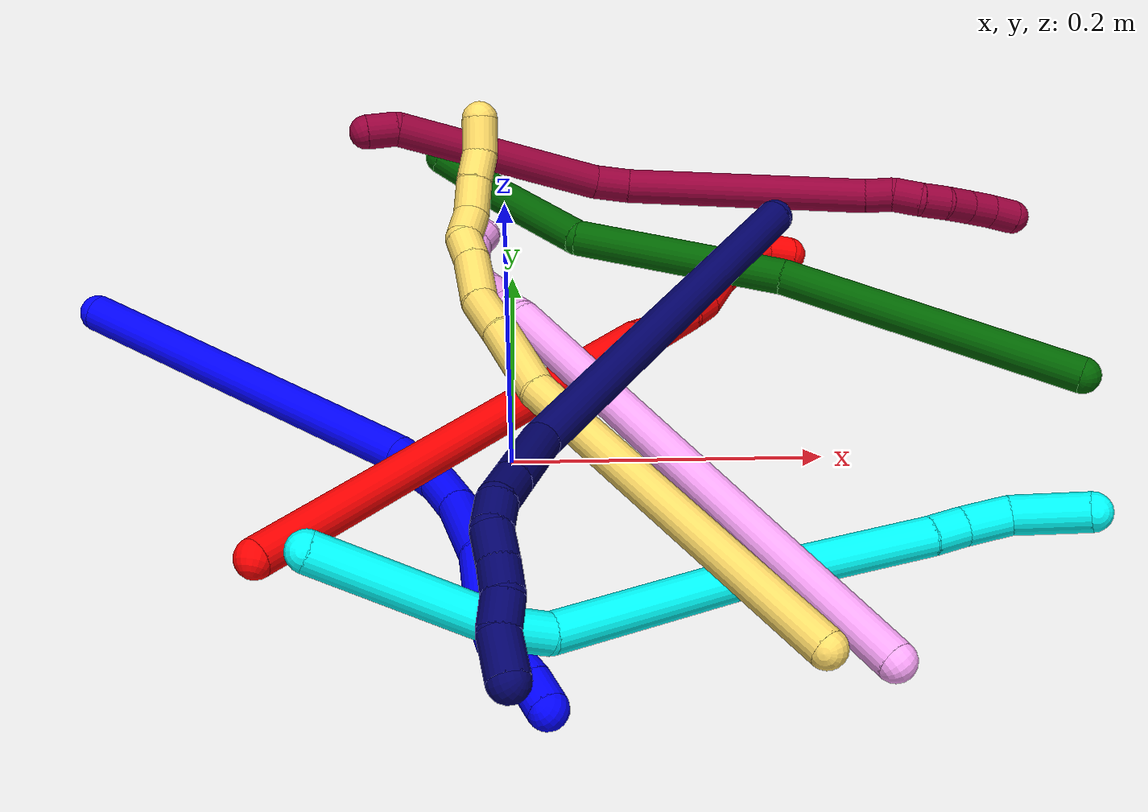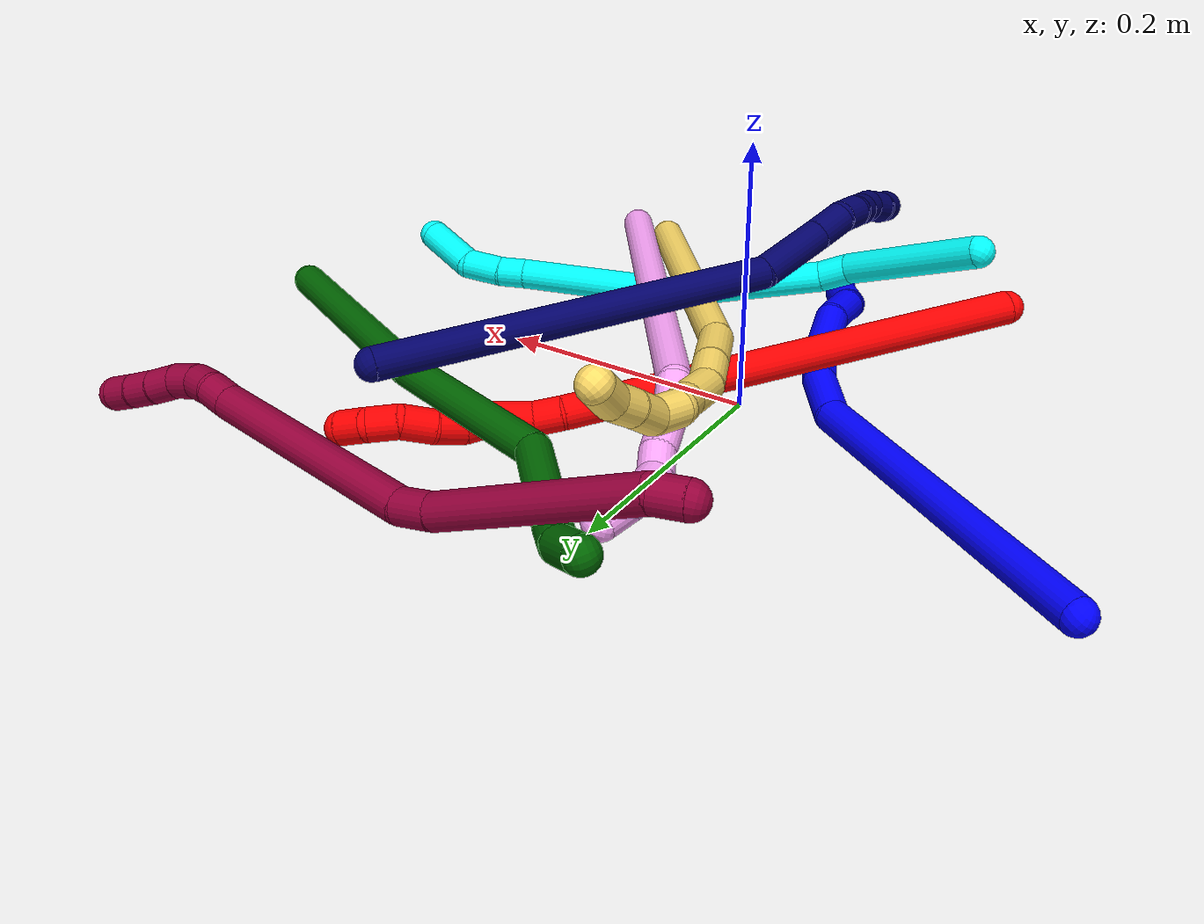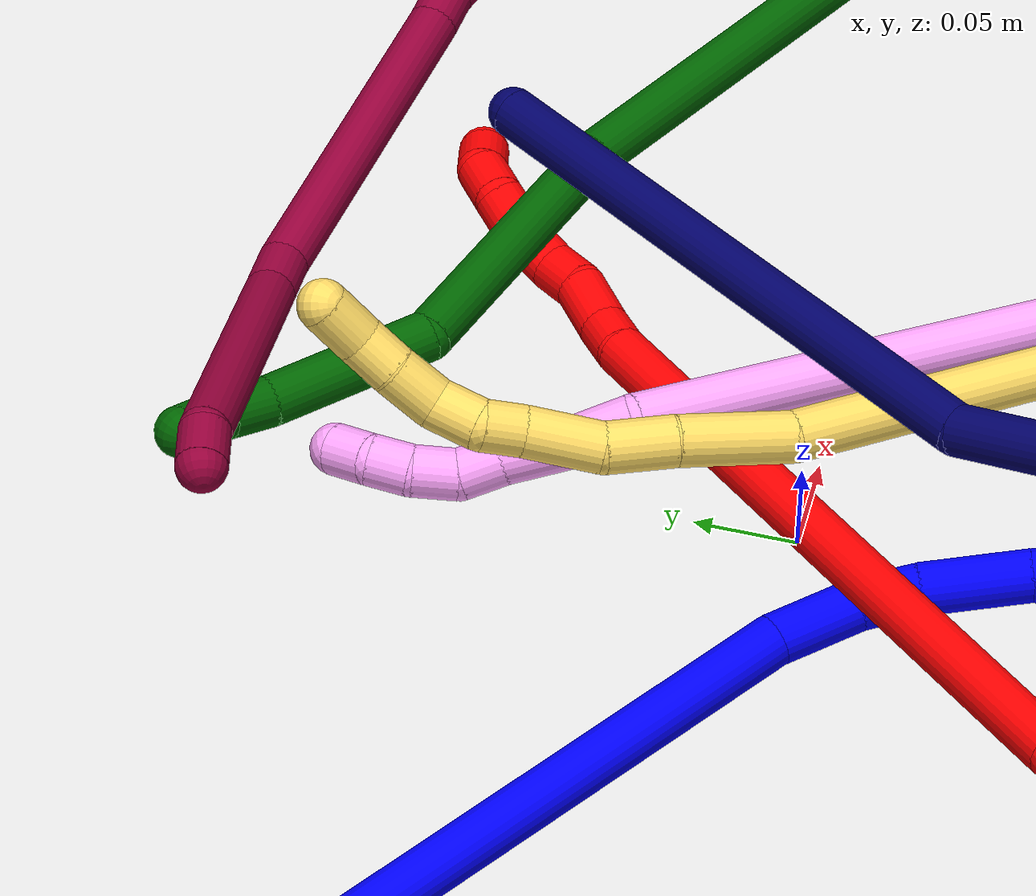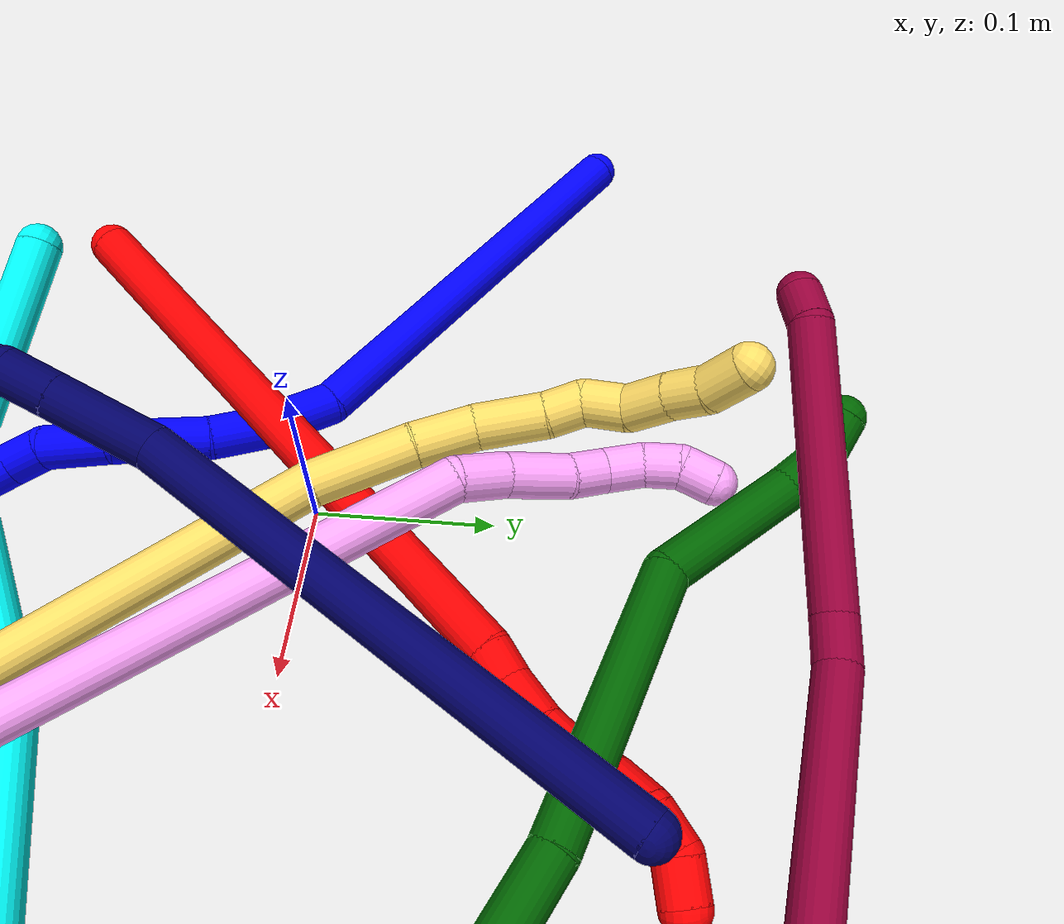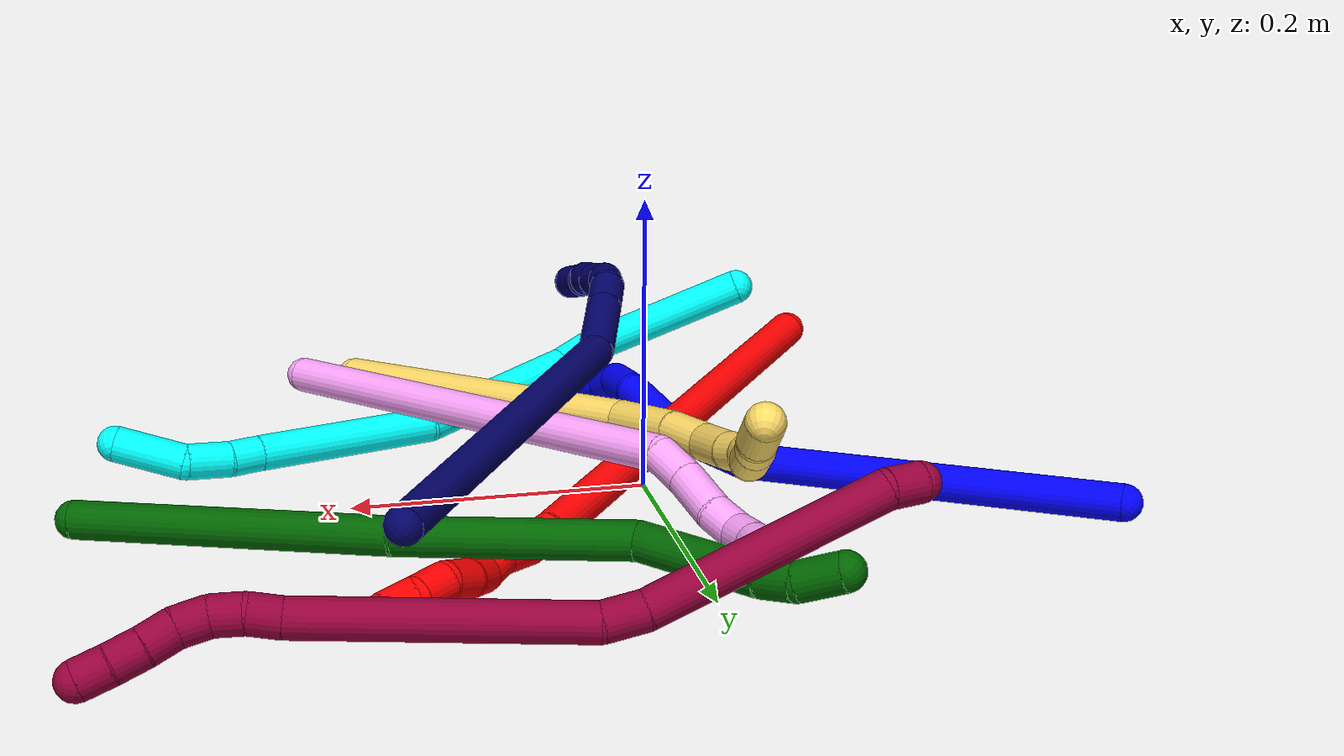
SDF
<sdf version="1.7">
 <world name="default">
  <plugin name="TubeGeneratorPlugin" filename="libtube_generator_plugin.so"/>
  <model name="photoneo_s_sensor">
   <static>1</static>
   <pose>0 0 2 1.57079 1.57079 3.14159</pose>
   <link name="link">
    <inertial><mass>0.1</mass></inertial>
    <sensor name="sensor" type="depth">
     <update_rate>30</update_rate>
     <camera>
      <horizontal_fov>1.22</horizontal_fov>
      <image><width>1920</width><height>1200</height><format>B8G8R8</format></image>
      <clip><near>0.1</near><far>4</far></clip>
      <depth_camera><output>points</output></depth_camera>
     </camera>
     <plugin name="camera_plugin" filename="libgazebo_ros_depth_camera.so">
      <baseline>0.2</baseline>
      <alwaysOn>1</alwaysOn>
      <updateRate>0.0</updateRate>
      <cameraName>camera_ir</cameraName>
      <imageTopicName>/camera/color/image_raw</imageTopicName>
      <cameraInfoTopicName>/camera/color/camera_info</cameraInfoTopicName>
      <depthImageTopicName>/camera/depth/image_raw</depthImageTopicName>
      <depthImageCameraInfoTopicName>/camera/depth/camera_info</depthImageCameraInfoTopicName>
      <pointCloudTopicName>/camera/depth/points</pointCloudTopicName>
      <frameName>fr_optical</frameName>
      <pointCloudCutoff>0.1</pointCloudCutoff>
      <pointCloudCutoffMax>2.0</pointCloudCutoffMax>
      <distortionK1>0</distortionK1>
      <distortionK2>0</distortionK2>
      <distortionK3>0</distortionK3>
      <distortionT1>0</distortionT1>
      <distortionT2>0</distortionT2>
      <CxPrime>0</CxPrime>
      <Cx>0</Cx>
      <Cy>0</Cy>
      <focalLength>0</focalLength>
      <hackBaseline>0</hackBaseline>
     </plugin>
    </sensor>
   </link>
  </model>
  <gravity>0 0 -9.8</gravity>
  <magnetic_field>6e-06 2.3e-05 -4.2e-05</magnetic_field>
  <atmosphere type="adiabatic"/>
  <physics name="default_physics" default="0" type="ode">
   <max_step_size>0.003</max_step_size>
   <real_time_factor>1</real_time_factor>
   <real_time_update_rate>1000</real_time_update_rate>
   <max_contacts>10000</max_contacts>
   <ode>
    <solver>
     <type>quick</type>
     <iters>100</iters>
     <sor>1.3</sor>
     <use_dynamic_moi_rescaling>0</use_dynamic_moi_rescaling>
    </solver>
    <constraints>
     <contact_max_correcting_vel>0</contact_max_correcting_vel>
     <contact_surface_layer>0.001</contact_surface_layer>
     <cfm>0</cfm>
     <erp>0.2</erp>
    </constraints>
   </ode>
  </physics>
  <scene><ambient>0.4 0.4 0.4 1</ambient><background>0.7 0.7 0.7 1</background><shadows>0</shadows></scene>
  <audio><device>default</device></audio>
  <spherical_coordinates>
   <surface_model>EARTH_WGS84</surface_model>
   <latitude_deg>0</latitude_deg>
   <longitude_deg>0</longitude_deg>
   <elevation>0</elevation>
   <heading_deg>0</heading_deg>
  </spherical_coordinates>
  <model name="bin">
   <static>1</static>
   <link name="bottom">
    <collision name="collision-bottom">
     <pose>0 0 -0.01 0 -0 0</pose>
     <geometry><box><size>0.8 0.6 0.02</size></box></geometry>
     <surface>
      <friction><ode><mu>100</mu><mu2>100</mu2></ode></friction>
      <contact><collide_bitmask>65535</collide_bitmask></contact>
     </surface>
    </collision>
   </link>
   <link name="west_wall">
    <collision name="collision-west_wall">
     <pose>-0.41 0 0.1 0 -0 0</pose>
     <geometry><box><size>0.02 0.6 0.2</size></box></geometry>
     <surface>
      <friction><ode><mu>100</mu><mu2>100</mu2></ode></friction>
      <contact><collide_bitmask>65535</collide_bitmask></contact>
     </surface>
    </collision>
   </link>
   <link name="east_wall">
    <collision name="collision-east_wall">
     <pose>0.41 0 0.1 0 -0 0</pose>
     <geometry><box><size>0.02 0.6 0.2</size></box></geometry>
     <surface>
      <friction><ode><mu>100</mu><mu2>100</mu2></ode></friction>
      <contact><collide_bitmask>65535</collide_bitmask></contact>
     </surface>
    </collision>
   </link>
   <link name="south_wall">
    <collision name="collision-south_wall">
     <pose>0 -0.31 0.1 0 -0 0</pose>
     <geometry><box><size>0.8 0.02 0.2</size></box></geometry>
     <surface>
      <friction><ode><mu>100</mu><mu2>100</mu2></ode></friction>
      <contact><collide_bitmask>65535</collide_bitmask></contact>
     </surface>
    </collision>
   </link>
   <link name="north_wall">
    <collision name="collision-north_wall">
     <pose>0 0.31 0.1 0 -0 0</pose>
     <geometry><box><size>0.8 0.02 0.2</size></box></geometry>
     <surface>
      <friction><ode><mu>100</mu><mu2>100</mu2></ode></friction>
      <contact><collide_bitmask>65535</collide_bitmask></contact>
     </surface>
    </collision>
   </link>
  </model>
  <model name="1">
   <static>0</static>
   <link name="1">
    <collision name="collision-cylinder-e_1_1_4">
     <pose>0.095829 -0.07199 -0.051151 2.18855 0.8262 1.40799</pose>
     <geometry><cylinder><radius>0.0125</radius><length>0.26063</length></cylinder></geometry>
     <surface>
      <friction><ode><mu>1.16</mu><mu2>1.16</mu2><slip1>0</slip1><slip2>0</slip2></ode></friction>
      <contact><ode><kp>1e+06</kp><kd>1</kd><max_vel>0</max_vel><min_depth>0.001</min_depth></ode></contact>
     </surface>
    </collision>
    <visual name="visual-cylinder-e_1_1_4">
     <pose>0.095829 -0.07199 -0.051151 2.18855 0.8262 1.40799</pose>
     <geometry><cylinder><radius>0.0125</radius><length>0.26063</length></cylinder></geometry>
     <material><ambient>0 0 1 1</ambient></material>
    </visual>
    <collision name="collision-cylinder-e_2_4_5">
     <pose>0.205826 -0.159693 -0.104485 1.70891 0.72897 0.826054</pose>
     <geometry><cylinder><radius>0.0125</radius><length>0.042541</length></cylinder></geometry>
     <surface>
      <friction><ode><mu>1.16</mu><mu2>1.16</mu2><slip1>0</slip1><slip2>0</slip2></ode></friction>
      <contact><ode><kp>1e+06</kp><kd>1</kd><max_vel>0</max_vel><min_depth>0.001</min_depth></ode></contact>
     </surface>
    </collision>
    <visual name="visual-cylinder-e_2_4_5">
     <pose>0.205826 -0.159693 -0.104485 1.70891 0.72897 0.826054</pose>
     <geometry><cylinder><radius>0.0125</radius><length>0.042541</length></cylinder></geometry>
     <material><ambient>0 0 1 1</ambient></material>
    </visual>
    <collision name="collision-cylinder-e_3_5_6">
     <pose>0.228117 -0.188164 -0.106372 1.54743 0.566825 0.554399</pose>
     <geometry><cylinder><radius>0.0125</radius><length>0.030253</length></cylinder></geometry>
     <surface>
      <friction><ode><mu>1.16</mu><mu2>1.16</mu2><slip1>0</slip1><slip2>0</slip2></ode></friction>
      <contact><ode><kp>1e+06</kp><kd>1</kd><max_vel>0</max_vel><min_depth>0.001</min_depth></ode></contact>
     </surface>
    </collision>
    <visual name="visual-cylinder-e_3_5_6">
     <pose>0.228117 -0.188164 -0.106372 1.54743 0.566825 0.554399</pose>
     <geometry><cylinder><radius>0.0125</radius><length>0.030253</length></cylinder></geometry>
     <material><ambient>0 0 1 1</ambient></material>
    </visual>
    <collision name="collision-cylinder-e_4_6_7">
     <pose>0.247284 -0.224417 -0.102277 1.41062 0.434493 0.371528</pose>
     <geometry><cylinder><radius>0.0125</radius><length>0.052475</length></cylinder></geometry>
     <surface>
      <friction><ode><mu>1.16</mu><mu2>1.16</mu2><slip1>0</slip1><slip2>0</slip2></ode></friction>
      <contact><ode><kp>1e+06</kp><kd>1</kd><max_vel>0</max_vel><min_depth>0.001</min_depth></ode></contact>
     </surface>
    </collision>
    <visual name="visual-cylinder-e_4_6_7">
     <pose>0.247284 -0.224417 -0.102277 1.41062 0.434493 0.371528</pose>
     <geometry><cylinder><radius>0.0125</radius><length>0.052475</length></cylinder></geometry>
     <material><ambient>0 0 1 1</ambient></material>
    </visual>
    <collision name="collision-cylinder-e_5_7_8">
     <pose>0.260987 -0.266748 -0.098061 1.54847 0.140158 0.137073</pose>
     <geometry><cylinder><radius>0.0125</radius><length>0.038056</length></cylinder></geometry>
     <surface>
      <friction><ode><mu>1.16</mu><mu2>1.16</mu2><slip1>0</slip1><slip2>0</slip2></ode></friction>
      <contact><ode><kp>1e+06</kp><kd>1</kd><max_vel>0</max_vel><min_depth>0.001</min_depth></ode></contact>
     </surface>
    </collision>
    <visual name="visual-cylinder-e_5_7_8">
     <pose>0.260987 -0.266748 -0.098061 1.54847 0.140158 0.137073</pose>
     <geometry><cylinder><radius>0.0125</radius><length>0.038056</length></cylinder></geometry>
     <material><ambient>0 0 1 1</ambient></material>
    </visual>
    <collision name="collision-cylinder-e_6_8_9">
     <pose>0.264899 -0.296117 -0.101452 1.91801 0.111552 0.158828</pose>
     <geometry><cylinder><radius>0.0125</radius><length>0.022541</length></cylinder></geometry>
     <surface>
      <friction><ode><mu>1.16</mu><mu2>1.16</mu2><slip1>0</slip1><slip2>0</slip2></ode></friction>
      <contact><ode><kp>1e+06</kp><kd>1</kd><max_vel>0</max_vel><min_depth>0.001</min_depth></ode></contact>
     </surface>
    </collision>
    <visual name="visual-cylinder-e_6_8_9">
     <pose>0.264899 -0.296117 -0.101452 1.91801 0.111552 0.158828</pose>
     <geometry><cylinder><radius>0.0125</radius><length>0.022541</length></cylinder></geometry>
     <material><ambient>0 0 1 1</ambient></material>
    </visual>
    <collision name="collision-cylinder-e_7_9_10">
     <pose>0.27428 -0.319984 -0.110182 1.92418 0.519395 0.7284</pose>
     <geometry><cylinder><radius>0.0125</radius><length>0.032744</length></cylinder></geometry>
     <surface>
      <friction><ode><mu>1.16</mu><mu2>1.16</mu2><slip1>0</slip1><slip2>0</slip2></ode></friction>
      <contact><ode><kp>1e+06</kp><kd>1</kd><max_vel>0</max_vel><min_depth>0.001</min_depth></ode></contact>
     </surface>
    </collision>
    <visual name="visual-cylinder-e_7_9_10">
     <pose>0.27428 -0.319984 -0.110182 1.92418 0.519395 0.7284</pose>
     <geometry><cylinder><radius>0.0125</radius><length>0.032744</length></cylinder></geometry>
     <material><ambient>0 0 1 1</ambient></material>
    </visual>
    <collision name="collision-cylinder-e_8_10_2">
     <pose>0.286867 -0.342562 -0.116648 1.73674 0.44416 0.521395</pose>
     <geometry><cylinder><radius>0.0125</radius><length>0.020759</length></cylinder></geometry>
     <surface>
      <friction><ode><mu>1.16</mu><mu2>1.16</mu2><slip1>0</slip1><slip2>0</slip2></ode></friction>
      <contact><ode><kp>1e+06</kp><kd>1</kd><max_vel>0</max_vel><min_depth>0.001</min_depth></ode></contact>
     </surface>
    </collision>
    <visual name="visual-cylinder-e_8_10_2">
     <pose>0.286867 -0.342562 -0.116648 1.73674 0.44416 0.521395</pose>
     <geometry><cylinder><radius>0.0125</radius><length>0.020759</length></cylinder></geometry>
     <material><ambient>0 0 1 1</ambient></material>
    </visual>
    <collision name="collision-sphere-2">
     <pose>0.291327 -0.351806 -0.118197 0 -0 0</pose>
     <geometry><sphere><radius>0.0125</radius></sphere></geometry>
     <surface>
      <friction><ode><mu>1.16</mu><mu2>1.16</mu2><slip1>0</slip1><slip2>0</slip2></ode></friction>
      <contact><ode><kp>1e+06</kp><kd>1</kd><max_vel>0</max_vel><min_depth>0.001</min_depth></ode></contact>
     </surface>
    </collision>
    <visual name="visual-sphere-2">
     <pose>0.291327 -0.351806 -0.118197 0 -0 0</pose>
     <geometry><sphere><radius>0.0125</radius></sphere></geometry>
     <material><ambient>0 0 1 1</ambient></material>
    </visual>
    <collision name="collision-sphere-10">
     <pose>0.282407 -0.333319 -0.1151 0 -0 0</pose>
     <geometry><sphere><radius>0.0125</radius></sphere></geometry>
     <surface>
      <friction><ode><mu>1.16</mu><mu2>1.16</mu2><slip1>0</slip1><slip2>0</slip2></ode></friction>
      <contact><ode><kp>1e+06</kp><kd>1</kd><max_vel>0</max_vel><min_depth>0.001</min_depth></ode></contact>
     </surface>
    </collision>
    <visual name="visual-sphere-10">
     <pose>0.282407 -0.333319 -0.1151 0 -0 0</pose>
     <geometry><sphere><radius>0.0125</radius></sphere></geometry>
     <material><ambient>0 0 1 1</ambient></material>
    </visual>
    <collision name="collision-sphere-9">
     <pose>0.266154 -0.306649 -0.105263 0 -0 0</pose>
     <geometry><sphere><radius>0.0125</radius></sphere></geometry>
     <surface>
      <friction><ode><mu>1.16</mu><mu2>1.16</mu2><slip1>0</slip1><slip2>0</slip2></ode></friction>
      <contact><ode><kp>1e+06</kp><kd>1</kd><max_vel>0</max_vel><min_depth>0.001</min_depth></ode></contact>
     </surface>
    </collision>
    <visual name="visual-sphere-9">
     <pose>0.266154 -0.306649 -0.105263 0 -0 0</pose>
     <geometry><sphere><radius>0.0125</radius></sphere></geometry>
     <material><ambient>0 0 1 1</ambient></material>
    </visual>
    <collision name="collision-sphere-4">
     <pose>0.191658 -0.143979 -0.102301 0 -0 0</pose>
     <geometry><sphere><radius>0.0125</radius></sphere></geometry>
     <surface>
      <friction><ode><mu>1.16</mu><mu2>1.16</mu2><slip1>0</slip1><slip2>0</slip2></ode></friction>
      <contact><ode><kp>1e+06</kp><kd>1</kd><max_vel>0</max_vel><min_depth>0.001</min_depth></ode></contact>
     </surface>
    </collision>
    <visual name="visual-sphere-4">
     <pose>0.191658 -0.143979 -0.102301 0 -0 0</pose>
     <geometry><sphere><radius>0.0125</radius></sphere></geometry>
     <material><ambient>0 0 1 1</ambient></material>
    </visual>
    <collision name="collision-sphere-1">
     <geometry><sphere><radius>0.0125</radius></sphere></geometry>
     <surface>
      <friction><ode><mu>1.16</mu><mu2>1.16</mu2><slip1>0</slip1><slip2>0</slip2></ode></friction>
      <contact><ode><kp>1e+06</kp><kd>1</kd><max_vel>0</max_vel><min_depth>0.001</min_depth></ode></contact>
     </surface>
    </collision>
    <visual name="visual-sphere-1">
     <geometry><sphere><radius>0.0125</radius></sphere></geometry>
     <material><ambient>0 0 1 1</ambient></material>
    </visual>
    <collision name="collision-sphere-8">
     <pose>0.263645 -0.285585 -0.09764 0 -0 0</pose>
     <geometry><sphere><radius>0.0125</radius></sphere></geometry>
     <surface>
      <friction><ode><mu>1.16</mu><mu2>1.16</mu2><slip1>0</slip1><slip2>0</slip2></ode></friction>
      <contact><ode><kp>1e+06</kp><kd>1</kd><max_vel>0</max_vel><min_depth>0.001</min_depth></ode></contact>
     </surface>
    </collision>
    <visual name="visual-sphere-8">
     <pose>0.263645 -0.285585 -0.09764 0 -0 0</pose>
     <geometry><sphere><radius>0.0125</radius></sphere></geometry>
     <material><ambient>0 0 1 1</ambient></material>
    </visual>
    <collision name="collision-sphere-5">
     <pose>0.219994 -0.175407 -0.10667 0 -0 0</pose>
     <geometry><sphere><radius>0.0125</radius></sphere></geometry>
     <surface>
      <friction><ode><mu>1.16</mu><mu2>1.16</mu2><slip1>0</slip1><slip2>0</slip2></ode></friction>
      <contact><ode><kp>1e+06</kp><kd>1</kd><max_vel>0</max_vel><min_depth>0.001</min_depth></ode></contact>
     </surface>
    </collision>
    <visual name="visual-sphere-5">
     <pose>0.219994 -0.175407 -0.10667 0 -0 0</pose>
     <geometry><sphere><radius>0.0125</radius></sphere></geometry>
     <material><ambient>0 0 1 1</ambient></material>
    </visual>
    <collision name="collision-sphere-6">
     <pose>0.236239 -0.200922 -0.106073 0 -0 0</pose>
     <geometry><sphere><radius>0.0125</radius></sphere></geometry>
     <surface>
      <friction><ode><mu>1.16</mu><mu2>1.16</mu2><slip1>0</slip1><slip2>0</slip2></ode></friction>
      <contact><ode><kp>1e+06</kp><kd>1</kd><max_vel>0</max_vel><min_depth>0.001</min_depth></ode></contact>
     </surface>
    </collision>
    <visual name="visual-sphere-6">
     <pose>0.236239 -0.200922 -0.106073 0 -0 0</pose>
     <geometry><sphere><radius>0.0125</radius></sphere></geometry>
     <material><ambient>0 0 1 1</ambient></material>
    </visual>
    <collision name="collision-sphere-7">
     <pose>0.258328 -0.247912 -0.098482 0 -0 0</pose>
     <geometry><sphere><radius>0.0125</radius></sphere></geometry>
     <surface>
      <friction><ode><mu>1.16</mu><mu2>1.16</mu2><slip1>0</slip1><slip2>0</slip2></ode></friction>
      <contact><ode><kp>1e+06</kp><kd>1</kd><max_vel>0</max_vel><min_depth>0.001</min_depth></ode></contact>
     </surface>
    </collision>
    <visual name="visual-sphere-7">
     <pose>0.258328 -0.247912 -0.098482 0 -0 0</pose>
     <geometry><sphere><radius>0.0125</radius></sphere></geometry>
     <material><ambient>0 0 1 1</ambient></material>
    </visual>
    <inertial>
     <pose>0.168898 -0.15488 -0.076819 0 -0 0</pose>
     <mass>0.5</mass>
     <inertia>
      <ixx>0.001224</ixx>
      <ixy>0</ixy>
      <ixz>0</ixz>
      <iyy>0.001728</iyy>
      <iyz>0</iyz>
      <izz>-0.000264</izz>
     </inertia>
    </inertial>
   </link>
   <pose>-0.28707 0.142126 0.018553 0.24173 -0.579222 -0.135498</pose>
  </model>
  <model name="2">
   <static>0</static>
   <link name="2">
    <collision name="collision-cylinder-e_1_1_4">
     <pose>0.078939 0.092921 0.11822 -0.666146 0.483425 -0.17017</pose>
     <geometry><cylinder><radius>0.0125</radius><length>0.339656</length></cylinder></geometry>
     <surface>
      <friction><ode><mu>1.16</mu><mu2>1.16</mu2><slip1>0</slip1><slip2>0</slip2></ode></friction>
      <contact><ode><kp>1e+06</kp><kd>1</kd><max_vel>0</max_vel><min_depth>0.001</min_depth></ode></contact>
     </surface>
    </collision>
    <visual name="visual-cylinder-e_1_1_4">
     <pose>0.078939 0.092921 0.11822 -0.666146 0.483425 -0.17017</pose>
     <geometry><cylinder><radius>0.0125</radius><length>0.339656</length></cylinder></geometry>
     <material><ambient>1 0 0 1</ambient></material>
    </visual>
    <collision name="collision-cylinder-e_2_4_5">
     <pose>0.164355 0.191728 0.242339 -0.784295 0.660799 -0.281804</pose>
     <geometry><cylinder><radius>0.0125</radius><length>0.021109</length></cylinder></geometry>
     <surface>
      <friction><ode><mu>1.16</mu><mu2>1.16</mu2><slip1>0</slip1><slip2>0</slip2></ode></friction>
      <contact><ode><kp>1e+06</kp><kd>1</kd><max_vel>0</max_vel><min_depth>0.001</min_depth></ode></contact>
     </surface>
    </collision>
    <visual name="visual-cylinder-e_2_4_5">
     <pose>0.164355 0.191728 0.242339 -0.784295 0.660799 -0.281804</pose>
     <geometry><cylinder><radius>0.0125</radius><length>0.021109</length></cylinder></geometry>
     <material><ambient>1 0 0 1</ambient></material>
    </visual>
    <collision name="collision-cylinder-e_3_5_6">
     <pose>0.179319 0.202529 0.258143 -0.460614 0.654575 -0.158867</pose>
     <geometry><cylinder><radius>0.0125</radius><length>0.027879</length></cylinder></geometry>
     <surface>
      <friction><ode><mu>1.16</mu><mu2>1.16</mu2><slip1>0</slip1><slip2>0</slip2></ode></friction>
      <contact><ode><kp>1e+06</kp><kd>1</kd><max_vel>0</max_vel><min_depth>0.001</min_depth></ode></contact>
     </surface>
    </collision>
    <visual name="visual-cylinder-e_3_5_6">
     <pose>0.179319 0.202529 0.258143 -0.460614 0.654575 -0.158867</pose>
     <geometry><cylinder><radius>0.0125</radius><length>0.027879</length></cylinder></geometry>
     <material><ambient>1 0 0 1</ambient></material>
    </visual>
    <collision name="collision-cylinder-e_4_6_7">
     <pose>0.192032 0.213576 0.275854 -0.665861 0.402486 -0.140857</pose>
     <geometry><cylinder><radius>0.0125</radius><length>0.021576</length></cylinder></geometry>
     <surface>
      <friction><ode><mu>1.16</mu><mu2>1.16</mu2><slip1>0</slip1><slip2>0</slip2></ode></friction>
      <contact><ode><kp>1e+06</kp><kd>1</kd><max_vel>0</max_vel><min_depth>0.001</min_depth></ode></contact>
     </surface>
    </collision>
    <visual name="visual-cylinder-e_4_6_7">
     <pose>0.192032 0.213576 0.275854 -0.665861 0.402486 -0.140857</pose>
     <geometry><cylinder><radius>0.0125</radius><length>0.021576</length></cylinder></geometry>
     <material><ambient>1 0 0 1</ambient></material>
    </visual>
    <collision name="collision-cylinder-e_5_7_8">
     <pose>0.199856 0.222271 0.293681 -0.250443 0.334862 -0.042544</pose>
     <geometry><cylinder><radius>0.0125</radius><length>0.021903</length></cylinder></geometry>
     <surface>
      <friction><ode><mu>1.16</mu><mu2>1.16</mu2><slip1>0</slip1><slip2>0</slip2></ode></friction>
      <contact><ode><kp>1e+06</kp><kd>1</kd><max_vel>0</max_vel><min_depth>0.001</min_depth></ode></contact>
     </surface>
    </collision>
    <visual name="visual-cylinder-e_5_7_8">
     <pose>0.199856 0.222271 0.293681 -0.250443 0.334862 -0.042544</pose>
     <geometry><cylinder><radius>0.0125</radius><length>0.021903</length></cylinder></geometry>
     <material><ambient>1 0 0 1</ambient></material>
    </visual>
    <collision name="collision-cylinder-e_6_8_9">
     <pose>0.209575 0.226808 0.313957 -0.190143 0.530007 -0.051747</pose>
     <geometry><cylinder><radius>0.0125</radius><length>0.02421</length></cylinder></geometry>
     <surface>
      <friction><ode><mu>1.16</mu><mu2>1.16</mu2><slip1>0</slip1><slip2>0</slip2></ode></friction>
      <contact><ode><kp>1e+06</kp><kd>1</kd><max_vel>0</max_vel><min_depth>0.001</min_depth></ode></contact>
     </surface>
    </collision>
    <visual name="visual-cylinder-e_6_8_9">
     <pose>0.209575 0.226808 0.313957 -0.190143 0.530007 -0.051747</pose>
     <geometry><cylinder><radius>0.0125</radius><length>0.02421</length></cylinder></geometry>
     <material><ambient>1 0 0 1</ambient></material>
    </visual>
    <collision name="collision-cylinder-e_7_9_10">
     <pose>0.222758 0.234042 0.331027 -0.657401 0.687169 -0.242854</pose>
     <geometry><cylinder><radius>0.0125</radius><length>0.022269</length></cylinder></geometry>
     <surface>
      <friction><ode><mu>1.16</mu><mu2>1.16</mu2><slip1>0</slip1><slip2>0</slip2></ode></friction>
      <contact><ode><kp>1e+06</kp><kd>1</kd><max_vel>0</max_vel><min_depth>0.001</min_depth></ode></contact>
     </surface>
    </collision>
    <visual name="visual-cylinder-e_7_9_10">
     <pose>0.222758 0.234042 0.331027 -0.657401 0.687169 -0.242854</pose>
     <geometry><cylinder><radius>0.0125</radius><length>0.022269</length></cylinder></geometry>
     <material><ambient>1 0 0 1</ambient></material>
    </visual>
    <collision name="collision-cylinder-e_8_10_2">
     <pose>0.238715 0.244888 0.339879 -1.22086 0.981373 -0.715355</pose>
     <geometry><cylinder><radius>0.0125</radius><length>0.021398</length></cylinder></geometry>
     <surface>
      <friction><ode><mu>1.16</mu><mu2>1.16</mu2><slip1>0</slip1><slip2>0</slip2></ode></friction>
      <contact><ode><kp>1e+06</kp><kd>1</kd><max_vel>0</max_vel><min_depth>0.001</min_depth></ode></contact>
     </surface>
    </collision>
    <visual name="visual-cylinder-e_8_10_2">
     <pose>0.238715 0.244888 0.339879 -1.22086 0.981373 -0.715355</pose>
     <geometry><cylinder><radius>0.0125</radius><length>0.021398</length></cylinder></geometry>
     <material><ambient>1 0 0 1</ambient></material>
    </visual>
    <collision name="collision-sphere-2">
     <pose>0.247608 0.250475 0.341918 0 -0 0</pose>
     <geometry><sphere><radius>0.0125</radius></sphere></geometry>
     <surface>
      <friction><ode><mu>1.16</mu><mu2>1.16</mu2><slip1>0</slip1><slip2>0</slip2></ode></friction>
      <contact><ode><kp>1e+06</kp><kd>1</kd><max_vel>0</max_vel><min_depth>0.001</min_depth></ode></contact>
     </surface>
    </collision>
    <visual name="visual-sphere-2">
     <pose>0.247608 0.250475 0.341918 0 -0 0</pose>
     <geometry><sphere><radius>0.0125</radius></sphere></geometry>
     <material><ambient>1 0 0 1</ambient></material>
    </visual>
    <collision name="collision-sphere-10">
     <pose>0.229821 0.239301 0.33784 0 -0 0</pose>
     <geometry><sphere><radius>0.0125</radius></sphere></geometry>
     <surface>
      <friction><ode><mu>1.16</mu><mu2>1.16</mu2><slip1>0</slip1><slip2>0</slip2></ode></friction>
      <contact><ode><kp>1e+06</kp><kd>1</kd><max_vel>0</max_vel><min_depth>0.001</min_depth></ode></contact>
     </surface>
    </collision>
    <visual name="visual-sphere-10">
     <pose>0.229821 0.239301 0.33784 0 -0 0</pose>
     <geometry><sphere><radius>0.0125</radius></sphere></geometry>
     <material><ambient>1 0 0 1</ambient></material>
    </visual>
    <collision name="collision-sphere-9">
     <pose>0.215695 0.228782 0.324213 0 -0 0</pose>
     <geometry><sphere><radius>0.0125</radius></sphere></geometry>
     <surface>
      <friction><ode><mu>1.16</mu><mu2>1.16</mu2><slip1>0</slip1><slip2>0</slip2></ode></friction>
      <contact><ode><kp>1e+06</kp><kd>1</kd><max_vel>0</max_vel><min_depth>0.001</min_depth></ode></contact>
     </surface>
    </collision>
    <visual name="visual-sphere-9">
     <pose>0.215695 0.228782 0.324213 0 -0 0</pose>
     <geometry><sphere><radius>0.0125</radius></sphere></geometry>
     <material><ambient>1 0 0 1</ambient></material>
    </visual>
    <collision name="collision-sphere-4">
     <pose>0.157877 0.185842 0.23644 0 -0 0</pose>
     <geometry><sphere><radius>0.0125</radius></sphere></geometry>
     <surface>
      <friction><ode><mu>1.16</mu><mu2>1.16</mu2><slip1>0</slip1><slip2>0</slip2></ode></friction>
      <contact><ode><kp>1e+06</kp><kd>1</kd><max_vel>0</max_vel><min_depth>0.001</min_depth></ode></contact>
     </surface>
    </collision>
    <visual name="visual-sphere-4">
     <pose>0.157877 0.185842 0.23644 0 -0 0</pose>
     <geometry><sphere><radius>0.0125</radius></sphere></geometry>
     <material><ambient>1 0 0 1</ambient></material>
    </visual>
    <collision name="collision-sphere-1">
     <geometry><sphere><radius>0.0125</radius></sphere></geometry>
     <surface>
      <friction><ode><mu>1.16</mu><mu2>1.16</mu2><slip1>0</slip1><slip2>0</slip2></ode></friction>
      <contact><ode><kp>1e+06</kp><kd>1</kd><max_vel>0</max_vel><min_depth>0.001</min_depth></ode></contact>
     </surface>
    </collision>
    <visual name="visual-sphere-1">
     <geometry><sphere><radius>0.0125</radius></sphere></geometry>
     <material><ambient>1 0 0 1</ambient></material>
    </visual>
    <collision name="collision-sphere-8">
     <pose>0.203456 0.224834 0.303702 0 -0 0</pose>
     <geometry><sphere><radius>0.0125</radius></sphere></geometry>
     <surface>
      <friction><ode><mu>1.16</mu><mu2>1.16</mu2><slip1>0</slip1><slip2>0</slip2></ode></friction>
      <contact><ode><kp>1e+06</kp><kd>1</kd><max_vel>0</max_vel><min_depth>0.001</min_depth></ode></contact>
     </surface>
    </collision>
    <visual name="visual-sphere-8">
     <pose>0.203456 0.224834 0.303702 0 -0 0</pose>
     <geometry><sphere><radius>0.0125</radius></sphere></geometry>
     <material><ambient>1 0 0 1</ambient></material>
    </visual>
    <collision name="collision-sphere-5">
     <pose>0.170833 0.197613 0.248237 0 -0 0</pose>
     <geometry><sphere><radius>0.0125</radius></sphere></geometry>
     <surface>
      <friction><ode><mu>1.16</mu><mu2>1.16</mu2><slip1>0</slip1><slip2>0</slip2></ode></friction>
      <contact><ode><kp>1e+06</kp><kd>1</kd><max_vel>0</max_vel><min_depth>0.001</min_depth></ode></contact>
     </surface>
    </collision>
    <visual name="visual-sphere-5">
     <pose>0.170833 0.197613 0.248237 0 -0 0</pose>
     <geometry><sphere><radius>0.0125</radius></sphere></geometry>
     <material><ambient>1 0 0 1</ambient></material>
    </visual>
    <collision name="collision-sphere-6">
     <pose>0.187806 0.207444 0.268049 0 -0 0</pose>
     <geometry><sphere><radius>0.0125</radius></sphere></geometry>
     <surface>
      <friction><ode><mu>1.16</mu><mu2>1.16</mu2><slip1>0</slip1><slip2>0</slip2></ode></friction>
      <contact><ode><kp>1e+06</kp><kd>1</kd><max_vel>0</max_vel><min_depth>0.001</min_depth></ode></contact>
     </surface>
    </collision>
    <visual name="visual-sphere-6">
     <pose>0.187806 0.207444 0.268049 0 -0 0</pose>
     <geometry><sphere><radius>0.0125</radius></sphere></geometry>
     <material><ambient>1 0 0 1</ambient></material>
    </visual>
    <collision name="collision-sphere-7">
     <pose>0.196257 0.219707 0.28366 0 -0 0</pose>
     <geometry><sphere><radius>0.0125</radius></sphere></geometry>
     <surface>
      <friction><ode><mu>1.16</mu><mu2>1.16</mu2><slip1>0</slip1><slip2>0</slip2></ode></friction>
      <contact><ode><kp>1e+06</kp><kd>1</kd><max_vel>0</max_vel><min_depth>0.001</min_depth></ode></contact>
     </surface>
    </collision>
    <visual name="visual-sphere-7">
     <pose>0.196257 0.219707 0.28366 0 -0 0</pose>
     <geometry><sphere><radius>0.0125</radius></sphere></geometry>
     <material><ambient>1 0 0 1</ambient></material>
    </visual>
    <inertial>
     <pose>0.117887 0.133348 0.174192 0 -0 0</pose>
     <mass>0.5</mass>
     <inertia>
      <ixx>0.002397</ixx>
      <ixy>0</ixy>
      <ixz>0</ixz>
      <iyy>0.002238</iyy>
      <iyz>0</iyz>
      <izz>-0.003304</izz>
     </inertia>
    </inertial>
   </link>
   <pose>-0.142946 -0.143036 0.059851 -1.08836 -0.0739 -0.23954</pose>
  </model>
  <model name="3">
   <static>0</static>
   <link name="3">
    <collision name="collision-cylinder-e_1_1_4">
     <pose>0.054699 -0.021203 -0.011577 2.07056 1.15492 1.66422</pose>
     <geometry><cylinder><radius>0.0125</radius><length>0.119592</length></cylinder></geometry>
     <surface>
      <friction><ode><mu>1.16</mu><mu2>1.16</mu2><slip1>0</slip1><slip2>0</slip2></ode></friction>
      <contact><ode><kp>1e+06</kp><kd>1</kd><max_vel>0</max_vel><min_depth>0.001</min_depth></ode></contact>
     </surface>
    </collision>
    <visual name="visual-cylinder-e_1_1_4">
     <pose>0.054699 -0.021203 -0.011577 2.07056 1.15492 1.66422</pose>
     <geometry><cylinder><radius>0.0125</radius><length>0.119592</length></cylinder></geometry>
     <material><ambient>0.003922 1 0.996078 1</ambient></material>
    </visual>
    <collision name="collision-cylinder-e_2_4_5">
     <pose>0.120354 -0.04411 -0.029008 2.85836 1.06292 2.66574</pose>
     <geometry><cylinder><radius>0.0125</radius><length>0.025077</length></cylinder></geometry>
     <surface>
      <friction><ode><mu>1.16</mu><mu2>1.16</mu2><slip1>0</slip1><slip2>0</slip2></ode></friction>
      <contact><ode><kp>1e+06</kp><kd>1</kd><max_vel>0</max_vel><min_depth>0.001</min_depth></ode></contact>
     </surface>
    </collision>
    <visual name="visual-cylinder-e_2_4_5">
     <pose>0.120354 -0.04411 -0.029008 2.85836 1.06292 2.66574</pose>
     <geometry><cylinder><radius>0.0125</radius><length>0.025077</length></cylinder></geometry>
     <material><ambient>0.003922 1 0.996078 1</ambient></material>
    </visual>
    <collision name="collision-cylinder-e_3_5_6">
     <pose>0.184173 -0.031986 -0.064291 -2.70233 1.01938 -2.38165</pose>
     <geometry><cylinder><radius>0.0125</radius><length>0.124125</length></cylinder></geometry>
     <surface>
      <friction><ode><mu>1.16</mu><mu2>1.16</mu2><slip1>0</slip1><slip2>0</slip2></ode></friction>
      <contact><ode><kp>1e+06</kp><kd>1</kd><max_vel>0</max_vel><min_depth>0.001</min_depth></ode></contact>
     </surface>
    </collision>
    <visual name="visual-cylinder-e_3_5_6">
     <pose>0.184173 -0.031986 -0.064291 -2.70233 1.01938 -2.38165</pose>
     <geometry><cylinder><radius>0.0125</radius><length>0.124125</length></cylinder></geometry>
     <material><ambient>0.003922 1 0.996078 1</ambient></material>
    </visual>
    <collision name="collision-cylinder-e_4_6_7">
     <pose>0.298265 -0.004604 -0.108514 -2.39995 1.2541 -2.15663</pose>
     <geometry><cylinder><radius>0.0125</radius><length>0.128865</length></cylinder></geometry>
     <surface>
      <friction><ode><mu>1.16</mu><mu2>1.16</mu2><slip1>0</slip1><slip2>0</slip2></ode></friction>
      <contact><ode><kp>1e+06</kp><kd>1</kd><max_vel>0</max_vel><min_depth>0.001</min_depth></ode></contact>
     </surface>
    </collision>
    <visual name="visual-cylinder-e_4_6_7">
     <pose>0.298265 -0.004604 -0.108514 -2.39995 1.2541 -2.15663</pose>
     <geometry><cylinder><radius>0.0125</radius><length>0.128865</length></cylinder></geometry>
     <material><ambient>0.003922 1 0.996078 1</ambient></material>
    </visual>
    <collision name="collision-cylinder-e_5_7_8">
     <pose>0.369751 0.011845 -0.126439 -2.39526 1.17692 -2.08046</pose>
     <geometry><cylinder><radius>0.0125</radius><length>0.022215</length></cylinder></geometry>
     <surface>
      <friction><ode><mu>1.16</mu><mu2>1.16</mu2><slip1>0</slip1><slip2>0</slip2></ode></friction>
      <contact><ode><kp>1e+06</kp><kd>1</kd><max_vel>0</max_vel><min_depth>0.001</min_depth></ode></contact>
     </surface>
    </collision>
    <visual name="visual-cylinder-e_5_7_8">
     <pose>0.369751 0.011845 -0.126439 -2.39526 1.17692 -2.08046</pose>
     <geometry><cylinder><radius>0.0125</radius><length>0.022215</length></cylinder></geometry>
     <material><ambient>0.003922 1 0.996078 1</ambient></material>
    </visual>
    <collision name="collision-cylinder-e_6_8_9">
     <pose>0.394953 0.018318 -0.131592 -2.08526 1.30234 -1.83472</pose>
     <geometry><cylinder><radius>0.0125</radius><length>0.031001</length></cylinder></geometry>
     <surface>
      <friction><ode><mu>1.16</mu><mu2>1.16</mu2><slip1>0</slip1><slip2>0</slip2></ode></friction>
      <contact><ode><kp>1e+06</kp><kd>1</kd><max_vel>0</max_vel><min_depth>0.001</min_depth></ode></contact>
     </surface>
    </collision>
    <visual name="visual-cylinder-e_6_8_9">
     <pose>0.394953 0.018318 -0.131592 -2.08526 1.30234 -1.83472</pose>
     <geometry><cylinder><radius>0.0125</radius><length>0.031001</length></cylinder></geometry>
     <material><ambient>0.003922 1 0.996078 1</ambient></material>
    </visual>
    <collision name="collision-cylinder-e_7_9_2">
     <pose>0.433162 0.023027 -0.125813 -0.143835 1.24408 -0.103216</pose>
     <geometry><cylinder><radius>0.0125</radius><length>0.049126</length></cylinder></geometry>
     <surface>
      <friction><ode><mu>1.16</mu><mu2>1.16</mu2><slip1>0</slip1><slip2>0</slip2></ode></friction>
      <contact><ode><kp>1e+06</kp><kd>1</kd><max_vel>0</max_vel><min_depth>0.001</min_depth></ode></contact>
     </surface>
    </collision>
    <visual name="visual-cylinder-e_7_9_2">
     <pose>0.433162 0.023027 -0.125813 -0.143835 1.24408 -0.103216</pose>
     <geometry><cylinder><radius>0.0125</radius><length>0.049126</length></cylinder></geometry>
     <material><ambient>0.003922 1 0.996078 1</ambient></material>
    </visual>
    <collision name="collision-sphere-2">
     <pose>0.456425 0.024157 -0.118012 0 -0 0</pose>
     <geometry><sphere><radius>0.0125</radius></sphere></geometry>
     <surface>
      <friction><ode><mu>1.16</mu><mu2>1.16</mu2><slip1>0</slip1><slip2>0</slip2></ode></friction>
      <contact><ode><kp>1e+06</kp><kd>1</kd><max_vel>0</max_vel><min_depth>0.001</min_depth></ode></contact>
     </surface>
    </collision>
    <visual name="visual-sphere-2">
     <pose>0.456425 0.024157 -0.118012 0 -0 0</pose>
     <geometry><sphere><radius>0.0125</radius></sphere></geometry>
     <material><ambient>0.003922 1 0.996078 1</ambient></material>
    </visual>
    <collision name="collision-sphere-9">
     <pose>0.409898 0.021897 -0.133615 0 -0 0</pose>
     <geometry><sphere><radius>0.0125</radius></sphere></geometry>
     <surface>
      <friction><ode><mu>1.16</mu><mu2>1.16</mu2><slip1>0</slip1><slip2>0</slip2></ode></friction>
      <contact><ode><kp>1e+06</kp><kd>1</kd><max_vel>0</max_vel><min_depth>0.001</min_depth></ode></contact>
     </surface>
    </collision>
    <visual name="visual-sphere-9">
     <pose>0.409898 0.021897 -0.133615 0 -0 0</pose>
     <geometry><sphere><radius>0.0125</radius></sphere></geometry>
     <material><ambient>0.003922 1 0.996078 1</ambient></material>
    </visual>
    <collision name="collision-sphere-4">
     <pose>0.109398 -0.042405 -0.023153 0 -0 0</pose>
     <geometry><sphere><radius>0.0125</radius></sphere></geometry>
     <surface>
      <friction><ode><mu>1.16</mu><mu2>1.16</mu2><slip1>0</slip1><slip2>0</slip2></ode></friction>
      <contact><ode><kp>1e+06</kp><kd>1</kd><max_vel>0</max_vel><min_depth>0.001</min_depth></ode></contact>
     </surface>
    </collision>
    <visual name="visual-sphere-4">
     <pose>0.109398 -0.042405 -0.023153 0 -0 0</pose>
     <geometry><sphere><radius>0.0125</radius></sphere></geometry>
     <material><ambient>0.003922 1 0.996078 1</ambient></material>
    </visual>
    <collision name="collision-sphere-1">
     <geometry><sphere><radius>0.0125</radius></sphere></geometry>
     <surface>
      <friction><ode><mu>1.16</mu><mu2>1.16</mu2><slip1>0</slip1><slip2>0</slip2></ode></friction>
      <contact><ode><kp>1e+06</kp><kd>1</kd><max_vel>0</max_vel><min_depth>0.001</min_depth></ode></contact>
     </surface>
    </collision>
    <visual name="visual-sphere-1">
     <geometry><sphere><radius>0.0125</radius></sphere></geometry>
     <material><ambient>0.003922 1 0.996078 1</ambient></material>
    </visual>
    <collision name="collision-sphere-8">
     <pose>0.380008 0.014739 -0.129569 0 -0 0</pose>
     <geometry><sphere><radius>0.0125</radius></sphere></geometry>
     <surface>
      <friction><ode><mu>1.16</mu><mu2>1.16</mu2><slip1>0</slip1><slip2>0</slip2></ode></friction>
      <contact><ode><kp>1e+06</kp><kd>1</kd><max_vel>0</max_vel><min_depth>0.001</min_depth></ode></contact>
     </surface>
    </collision>
    <visual name="visual-sphere-8">
     <pose>0.380008 0.014739 -0.129569 0 -0 0</pose>
     <geometry><sphere><radius>0.0125</radius></sphere></geometry>
     <material><ambient>0.003922 1 0.996078 1</ambient></material>
    </visual>
    <collision name="collision-sphere-5">
     <pose>0.13131 -0.045814 -0.034863 0 -0 0</pose>
     <geometry><sphere><radius>0.0125</radius></sphere></geometry>
     <surface>
      <friction><ode><mu>1.16</mu><mu2>1.16</mu2><slip1>0</slip1><slip2>0</slip2></ode></friction>
      <contact><ode><kp>1e+06</kp><kd>1</kd><max_vel>0</max_vel><min_depth>0.001</min_depth></ode></contact>
     </surface>
    </collision>
    <visual name="visual-sphere-5">
     <pose>0.13131 -0.045814 -0.034863 0 -0 0</pose>
     <geometry><sphere><radius>0.0125</radius></sphere></geometry>
     <material><ambient>0.003922 1 0.996078 1</ambient></material>
    </visual>
    <collision name="collision-sphere-6">
     <pose>0.237037 -0.018159 -0.093718 0 -0 0</pose>
     <geometry><sphere><radius>0.0125</radius></sphere></geometry>
     <surface>
      <friction><ode><mu>1.16</mu><mu2>1.16</mu2><slip1>0</slip1><slip2>0</slip2></ode></friction>
      <contact><ode><kp>1e+06</kp><kd>1</kd><max_vel>0</max_vel><min_depth>0.001</min_depth></ode></contact>
     </surface>
    </collision>
    <visual name="visual-sphere-6">
     <pose>0.237037 -0.018159 -0.093718 0 -0 0</pose>
     <geometry><sphere><radius>0.0125</radius></sphere></geometry>
     <material><ambient>0.003922 1 0.996078 1</ambient></material>
    </visual>
    <collision name="collision-sphere-7">
     <pose>0.359494 0.00895 -0.123309 0 -0 0</pose>
     <geometry><sphere><radius>0.0125</radius></sphere></geometry>
     <surface>
      <friction><ode><mu>1.16</mu><mu2>1.16</mu2><slip1>0</slip1><slip2>0</slip2></ode></friction>
      <contact><ode><kp>1e+06</kp><kd>1</kd><max_vel>0</max_vel><min_depth>0.001</min_depth></ode></contact>
     </surface>
    </collision>
    <visual name="visual-sphere-7">
     <pose>0.359494 0.00895 -0.123309 0 -0 0</pose>
     <geometry><sphere><radius>0.0125</radius></sphere></geometry>
     <material><ambient>0.003922 1 0.996078 1</ambient></material>
    </visual>
    <inertial>
     <pose>0.225187 -0.012486 -0.074289 0 -0 0</pose>
     <mass>0.5</mass>
     <inertia>
      <ixx>-0.000111</ixx>
      <ixy>0</ixy>
      <ixz>0</ixz>
      <iyy>0.000418</iyy>
      <iyz>0</iyz>
      <izz>-0.000501</izz>
     </inertia>
    </inertial>
   </link>
   <pose>-0.109434 -0.16703 0.088107 0.808136 -0.007237 -0.041893</pose>
  </model>
  <model name="4">
   <static>0</static>
   <link name="4">
    <collision name="collision-cylinder-e_1_1_4">
     <pose>-0.054827 0.166157 0.01275 -1.49421 -0.317851 0.294747</pose>
     <geometry><cylinder><radius>0.0125</radius><length>0.350865</length></cylinder></geometry>
     <surface>
      <friction><ode><mu>1.16</mu><mu2>1.16</mu2><slip1>0</slip1><slip2>0</slip2></ode></friction>
      <contact><ode><kp>1e+06</kp><kd>1</kd><max_vel>0</max_vel><min_depth>0.001</min_depth></ode></contact>
     </surface>
    </collision>
    <visual name="visual-cylinder-e_1_1_4">
     <pose>-0.054827 0.166157 0.01275 -1.49421 -0.317851 0.294747</pose>
     <geometry><cylinder><radius>0.0125</radius><length>0.350865</length></cylinder></geometry>
     <material><ambient>1 0.65098 0.996078 1</ambient></material>
    </visual>
    <collision name="collision-cylinder-e_2_4_5">
     <pose>-0.119314 0.342632 0.026192 -1.50378 -0.75132 0.706659</pose>
     <geometry><cylinder><radius>0.0125</radius><length>0.028303</length></cylinder></geometry>
     <surface>
      <friction><ode><mu>1.16</mu><mu2>1.16</mu2><slip1>0</slip1><slip2>0</slip2></ode></friction>
      <contact><ode><kp>1e+06</kp><kd>1</kd><max_vel>0</max_vel><min_depth>0.001</min_depth></ode></contact>
     </surface>
    </collision>
    <visual name="visual-cylinder-e_2_4_5">
     <pose>-0.119314 0.342632 0.026192 -1.50378 -0.75132 0.706659</pose>
     <geometry><cylinder><radius>0.0125</radius><length>0.028303</length></cylinder></geometry>
     <material><ambient>1 0.65098 0.996078 1</ambient></material>
    </visual>
    <collision name="collision-cylinder-e_3_5_6">
     <pose>-0.141827 0.365584 0.025256 -1.69898 -0.78986 0.885265</pose>
     <geometry><cylinder><radius>0.0125</radius><length>0.036192</length></cylinder></geometry>
     <surface>
      <friction><ode><mu>1.16</mu><mu2>1.16</mu2><slip1>0</slip1><slip2>0</slip2></ode></friction>
      <contact><ode><kp>1e+06</kp><kd>1</kd><max_vel>0</max_vel><min_depth>0.001</min_depth></ode></contact>
     </surface>
    </collision>
    <visual name="visual-cylinder-e_3_5_6">
     <pose>-0.141827 0.365584 0.025256 -1.69898 -0.78986 0.885265</pose>
     <geometry><cylinder><radius>0.0125</radius><length>0.036192</length></cylinder></geometry>
     <material><ambient>1 0.65098 0.996078 1</ambient></material>
    </visual>
    <collision name="collision-cylinder-e_4_6_7">
     <pose>-0.161712 0.386736 0.024265 -1.4961 -0.688771 0.642612</pose>
     <geometry><cylinder><radius>0.0125</radius><length>0.022127</length></cylinder></geometry>
     <surface>
      <friction><ode><mu>1.16</mu><mu2>1.16</mu2><slip1>0</slip1><slip2>0</slip2></ode></friction>
      <contact><ode><kp>1e+06</kp><kd>1</kd><max_vel>0</max_vel><min_depth>0.001</min_depth></ode></contact>
     </surface>
    </collision>
    <visual name="visual-cylinder-e_4_6_7">
     <pose>-0.161712 0.386736 0.024265 -1.4961 -0.688771 0.642612</pose>
     <geometry><cylinder><radius>0.0125</radius><length>0.022127</length></cylinder></geometry>
     <material><ambient>1 0.65098 0.996078 1</ambient></material>
    </visual>
    <collision name="collision-cylinder-e_5_7_8">
     <pose>-0.173424 0.404753 0.02148 -1.91657 -0.434087 0.608196</pose>
     <geometry><cylinder><radius>0.0125</radius><length>0.022258</length></cylinder></geometry>
     <surface>
      <friction><ode><mu>1.16</mu><mu2>1.16</mu2><slip1>0</slip1><slip2>0</slip2></ode></friction>
      <contact><ode><kp>1e+06</kp><kd>1</kd><max_vel>0</max_vel><min_depth>0.001</min_depth></ode></contact>
     </surface>
    </collision>
    <visual name="visual-cylinder-e_5_7_8">
     <pose>-0.173424 0.404753 0.02148 -1.91657 -0.434087 0.608196</pose>
     <geometry><cylinder><radius>0.0125</radius><length>0.022258</length></cylinder></geometry>
     <material><ambient>1 0.65098 0.996078 1</ambient></material>
    </visual>
    <collision name="collision-cylinder-e_6_8_9">
     <pose>-0.182752 0.421529 0.012871 -2.19004 -0.479521 0.886003</pose>
     <geometry><cylinder><radius>0.0125</radius><length>0.020145</length></cylinder></geometry>
     <surface>
      <friction><ode><mu>1.16</mu><mu2>1.16</mu2><slip1>0</slip1><slip2>0</slip2></ode></friction>
      <contact><ode><kp>1e+06</kp><kd>1</kd><max_vel>0</max_vel><min_depth>0.001</min_depth></ode></contact>
     </surface>
    </collision>
    <visual name="visual-cylinder-e_6_8_9">
     <pose>-0.182752 0.421529 0.012871 -2.19004 -0.479521 0.886003</pose>
     <geometry><cylinder><radius>0.0125</radius><length>0.020145</length></cylinder></geometry>
     <material><ambient>1 0.65098 0.996078 1</ambient></material>
    </visual>
    <collision name="collision-cylinder-e_7_9_2">
     <pose>-0.194313 0.432943 0.001669 -2.53924 -0.75828 1.81717</pose>
     <geometry><cylinder><radius>0.0125</radius><length>0.020109</length></cylinder></geometry>
     <surface>
      <friction><ode><mu>1.16</mu><mu2>1.16</mu2><slip1>0</slip1><slip2>0</slip2></ode></friction>
      <contact><ode><kp>1e+06</kp><kd>1</kd><max_vel>0</max_vel><min_depth>0.001</min_depth></ode></contact>
     </surface>
    </collision>
    <visual name="visual-cylinder-e_7_9_2">
     <pose>-0.194313 0.432943 0.001669 -2.53924 -0.75828 1.81717</pose>
     <geometry><cylinder><radius>0.0125</radius><length>0.020109</length></cylinder></geometry>
     <material><ambient>1 0.65098 0.996078 1</ambient></material>
    </visual>
    <collision name="collision-sphere-2">
     <pose>-0.201227 0.437079 -0.004346 0 -0 0</pose>
     <geometry><sphere><radius>0.0125</radius></sphere></geometry>
     <surface>
      <friction><ode><mu>1.16</mu><mu2>1.16</mu2><slip1>0</slip1><slip2>0</slip2></ode></friction>
      <contact><ode><kp>1e+06</kp><kd>1</kd><max_vel>0</max_vel><min_depth>0.001</min_depth></ode></contact>
     </surface>
    </collision>
    <visual name="visual-sphere-2">
     <pose>-0.201227 0.437079 -0.004346 0 -0 0</pose>
     <geometry><sphere><radius>0.0125</radius></sphere></geometry>
     <material><ambient>1 0.65098 0.996078 1</ambient></material>
    </visual>
    <collision name="collision-sphere-9">
     <pose>-0.187399 0.428807 0.007684 0 -0 0</pose>
     <geometry><sphere><radius>0.0125</radius></sphere></geometry>
     <surface>
      <friction><ode><mu>1.16</mu><mu2>1.16</mu2><slip1>0</slip1><slip2>0</slip2></ode></friction>
      <contact><ode><kp>1e+06</kp><kd>1</kd><max_vel>0</max_vel><min_depth>0.001</min_depth></ode></contact>
     </surface>
    </collision>
    <visual name="visual-sphere-9">
     <pose>-0.187399 0.428807 0.007684 0 -0 0</pose>
     <geometry><sphere><radius>0.0125</radius></sphere></geometry>
     <material><ambient>1 0.65098 0.996078 1</ambient></material>
    </visual>
    <collision name="collision-sphere-4">
     <pose>-0.109654 0.332313 0.025499 0 -0 0</pose>
     <geometry><sphere><radius>0.0125</radius></sphere></geometry>
     <surface>
      <friction><ode><mu>1.16</mu><mu2>1.16</mu2><slip1>0</slip1><slip2>0</slip2></ode></friction>
      <contact><ode><kp>1e+06</kp><kd>1</kd><max_vel>0</max_vel><min_depth>0.001</min_depth></ode></contact>
     </surface>
    </collision>
    <visual name="visual-sphere-4">
     <pose>-0.109654 0.332313 0.025499 0 -0 0</pose>
     <geometry><sphere><radius>0.0125</radius></sphere></geometry>
     <material><ambient>1 0.65098 0.996078 1</ambient></material>
    </visual>
    <collision name="collision-sphere-1">
     <geometry><sphere><radius>0.0125</radius></sphere></geometry>
     <surface>
      <friction><ode><mu>1.16</mu><mu2>1.16</mu2><slip1>0</slip1><slip2>0</slip2></ode></friction>
      <contact><ode><kp>1e+06</kp><kd>1</kd><max_vel>0</max_vel><min_depth>0.001</min_depth></ode></contact>
     </surface>
    </collision>
    <visual name="visual-sphere-1">
     <geometry><sphere><radius>0.0125</radius></sphere></geometry>
     <material><ambient>1 0.65098 0.996078 1</ambient></material>
    </visual>
    <collision name="collision-sphere-8">
     <pose>-0.178105 0.414252 0.018058 0 -0 0</pose>
     <geometry><sphere><radius>0.0125</radius></sphere></geometry>
     <surface>
      <friction><ode><mu>1.16</mu><mu2>1.16</mu2><slip1>0</slip1><slip2>0</slip2></ode></friction>
      <contact><ode><kp>1e+06</kp><kd>1</kd><max_vel>0</max_vel><min_depth>0.001</min_depth></ode></contact>
     </surface>
    </collision>
    <visual name="visual-sphere-8">
     <pose>-0.178105 0.414252 0.018058 0 -0 0</pose>
     <geometry><sphere><radius>0.0125</radius></sphere></geometry>
     <material><ambient>1 0.65098 0.996078 1</ambient></material>
    </visual>
    <collision name="collision-sphere-5">
     <pose>-0.128974 0.35295 0.026884 0 -0 0</pose>
     <geometry><sphere><radius>0.0125</radius></sphere></geometry>
     <surface>
      <friction><ode><mu>1.16</mu><mu2>1.16</mu2><slip1>0</slip1><slip2>0</slip2></ode></friction>
      <contact><ode><kp>1e+06</kp><kd>1</kd><max_vel>0</max_vel><min_depth>0.001</min_depth></ode></contact>
     </surface>
    </collision>
    <visual name="visual-sphere-5">
     <pose>-0.128974 0.35295 0.026884 0 -0 0</pose>
     <geometry><sphere><radius>0.0125</radius></sphere></geometry>
     <material><ambient>1 0.65098 0.996078 1</ambient></material>
    </visual>
    <collision name="collision-sphere-6">
     <pose>-0.15468 0.378219 0.023628 0 -0 0</pose>
     <geometry><sphere><radius>0.0125</radius></sphere></geometry>
     <surface>
      <friction><ode><mu>1.16</mu><mu2>1.16</mu2><slip1>0</slip1><slip2>0</slip2></ode></friction>
      <contact><ode><kp>1e+06</kp><kd>1</kd><max_vel>0</max_vel><min_depth>0.001</min_depth></ode></contact>
     </surface>
    </collision>
    <visual name="visual-sphere-6">
     <pose>-0.15468 0.378219 0.023628 0 -0 0</pose>
     <geometry><sphere><radius>0.0125</radius></sphere></geometry>
     <material><ambient>1 0.65098 0.996078 1</ambient></material>
    </visual>
    <collision name="collision-sphere-7">
     <pose>-0.168744 0.395254 0.024902 0 -0 0</pose>
     <geometry><sphere><radius>0.0125</radius></sphere></geometry>
     <surface>
      <friction><ode><mu>1.16</mu><mu2>1.16</mu2><slip1>0</slip1><slip2>0</slip2></ode></friction>
      <contact><ode><kp>1e+06</kp><kd>1</kd><max_vel>0</max_vel><min_depth>0.001</min_depth></ode></contact>
     </surface>
    </collision>
    <visual name="visual-sphere-7">
     <pose>-0.168744 0.395254 0.024902 0 -0 0</pose>
     <geometry><sphere><radius>0.0125</radius></sphere></geometry>
     <material><ambient>1 0.65098 0.996078 1</ambient></material>
    </visual>
    <inertial>
     <pose>-0.085549 0.231983 0.014873 0 -0 0</pose>
     <mass>0.5</mass>
     <inertia>
      <ixx>0.004281</ixx>
      <ixy>0</ixy>
      <ixz>0</ixz>
      <iyy>0.001636</iyy>
      <iyz>0</iyz>
      <izz>-0.002294</izz>
     </inertia>
    </inertial>
   </link>
   <pose>0.2126 -0.202061 0.029559 2.31997 -1.0227 -1.7227</pose>
  </model>
  <model name="5">
   <static>0</static>
   <link name="5">
    <collision name="collision-cylinder-e_1_1_4">
     <pose>-0.063066 0.097629 0.054524 -1.06146 -0.513518 0.305781</pose>
     <geometry><cylinder><radius>0.0125</radius><length>0.256761</length></cylinder></geometry>
     <surface>
      <friction><ode><mu>1.16</mu><mu2>1.16</mu2><slip1>0</slip1><slip2>0</slip2></ode></friction>
      <contact><ode><kp>1e+06</kp><kd>1</kd><max_vel>0</max_vel><min_depth>0.001</min_depth></ode></contact>
     </surface>
    </collision>
    <visual name="visual-cylinder-e_1_1_4">
     <pose>-0.063066 0.097629 0.054524 -1.06146 -0.513518 0.305781</pose>
     <geometry><cylinder><radius>0.0125</radius><length>0.256761</length></cylinder></geometry>
     <material><ambient>1 0.858824 0.4 1</ambient></material>
    </visual>
    <collision name="collision-cylinder-e_2_4_5">
     <pose>-0.142777 0.211762 0.124593 -0.815349 -0.633254 0.281137</pose>
     <geometry><cylinder><radius>0.0125</radius><length>0.056252</length></cylinder></geometry>
     <surface>
      <friction><ode><mu>1.16</mu><mu2>1.16</mu2><slip1>0</slip1><slip2>0</slip2></ode></friction>
      <contact><ode><kp>1e+06</kp><kd>1</kd><max_vel>0</max_vel><min_depth>0.001</min_depth></ode></contact>
     </surface>
    </collision>
    <visual name="visual-cylinder-e_2_4_5">
     <pose>-0.142777 0.211762 0.124593 -0.815349 -0.633254 0.281137</pose>
     <geometry><cylinder><radius>0.0125</radius><length>0.056252</length></cylinder></geometry>
     <material><ambient>1 0.858824 0.4 1</ambient></material>
    </visual>
    <collision name="collision-cylinder-e_3_5_6">
     <pose>-0.168007 0.238383 0.150657 -0.76586 -0.531795 0.218536</pose>
     <geometry><cylinder><radius>0.0125</radius><length>0.033864</length></cylinder></geometry>
     <surface>
      <friction><ode><mu>1.16</mu><mu2>1.16</mu2><slip1>0</slip1><slip2>0</slip2></ode></friction>
      <contact><ode><kp>1e+06</kp><kd>1</kd><max_vel>0</max_vel><min_depth>0.001</min_depth></ode></contact>
     </surface>
    </collision>
    <visual name="visual-cylinder-e_3_5_6">
     <pose>-0.168007 0.238383 0.150657 -0.76586 -0.531795 0.218536</pose>
     <geometry><cylinder><radius>0.0125</radius><length>0.033864</length></cylinder></geometry>
     <material><ambient>1 0.858824 0.4 1</ambient></material>
    </visual>
    <collision name="collision-cylinder-e_4_6_7">
     <pose>-0.189242 0.254898 0.173854 -0.467475 -0.727643 0.180821</pose>
     <geometry><cylinder><radius>0.0125</radius><length>0.038037</length></cylinder></geometry>
     <surface>
      <friction><ode><mu>1.16</mu><mu2>1.16</mu2><slip1>0</slip1><slip2>0</slip2></ode></friction>
      <contact><ode><kp>1e+06</kp><kd>1</kd><max_vel>0</max_vel><min_depth>0.001</min_depth></ode></contact>
     </surface>
    </collision>
    <visual name="visual-cylinder-e_4_6_7">
     <pose>-0.189242 0.254898 0.173854 -0.467475 -0.727643 0.180821</pose>
     <geometry><cylinder><radius>0.0125</radius><length>0.038037</length></cylinder></geometry>
     <material><ambient>1 0.858824 0.4 1</ambient></material>
    </visual>
    <collision name="collision-cylinder-e_5_7_8">
     <pose>-0.208978 0.265912 0.192187 -0.684332 -0.770656 0.286947</pose>
     <geometry><cylinder><radius>0.0125</radius><length>0.020344</length></cylinder></geometry>
     <surface>
      <friction><ode><mu>1.16</mu><mu2>1.16</mu2><slip1>0</slip1><slip2>0</slip2></ode></friction>
      <contact><ode><kp>1e+06</kp><kd>1</kd><max_vel>0</max_vel><min_depth>0.001</min_depth></ode></contact>
     </surface>
    </collision>
    <visual name="visual-cylinder-e_5_7_8">
     <pose>-0.208978 0.265912 0.192187 -0.684332 -0.770656 0.286947</pose>
     <geometry><cylinder><radius>0.0125</radius><length>0.020344</length></cylinder></geometry>
     <material><ambient>1 0.858824 0.4 1</ambient></material>
    </visual>
    <collision name="collision-cylinder-e_6_8_9">
     <pose>-0.223391 0.270553 0.207158 -0.003028 -0.666433 0.001048</pose>
     <geometry><cylinder><radius>0.0125</radius><length>0.023706</length></cylinder></geometry>
     <surface>
      <friction><ode><mu>1.16</mu><mu2>1.16</mu2><slip1>0</slip1><slip2>0</slip2></ode></friction>
      <contact><ode><kp>1e+06</kp><kd>1</kd><max_vel>0</max_vel><min_depth>0.001</min_depth></ode></contact>
     </surface>
    </collision>
    <visual name="visual-cylinder-e_6_8_9">
     <pose>-0.223391 0.270553 0.207158 -0.003028 -0.666433 0.001048</pose>
     <geometry><cylinder><radius>0.0125</radius><length>0.023706</length></cylinder></geometry>
     <material><ambient>1 0.858824 0.4 1</ambient></material>
    </visual>
    <collision name="collision-cylinder-e_7_9_10">
     <pose>-0.24231 0.270718 0.221625 -0.02658 -1.15263 0.017275</pose>
     <geometry><cylinder><radius>0.0125</radius><length>0.02537</length></cylinder></geometry>
     <surface>
      <friction><ode><mu>1.16</mu><mu2>1.16</mu2><slip1>0</slip1><slip2>0</slip2></ode></friction>
      <contact><ode><kp>1e+06</kp><kd>1</kd><max_vel>0</max_vel><min_depth>0.001</min_depth></ode></contact>
     </surface>
    </collision>
    <visual name="visual-cylinder-e_7_9_10">
     <pose>-0.24231 0.270718 0.221625 -0.02658 -1.15263 0.017275</pose>
     <geometry><cylinder><radius>0.0125</radius><length>0.02537</length></cylinder></geometry>
     <material><ambient>1 0.858824 0.4 1</ambient></material>
    </visual>
    <collision name="collision-cylinder-e_8_10_11">
     <pose>-0.263174 0.269966 0.231587 0.182699 -1.08506 -0.11034</pose>
     <geometry><cylinder><radius>0.0125</radius><length>0.02097</length></cylinder></geometry>
     <surface>
      <friction><ode><mu>1.16</mu><mu2>1.16</mu2><slip1>0</slip1><slip2>0</slip2></ode></friction>
      <contact><ode><kp>1e+06</kp><kd>1</kd><max_vel>0</max_vel><min_depth>0.001</min_depth></ode></contact>
     </surface>
    </collision>
    <visual name="visual-cylinder-e_8_10_11">
     <pose>-0.263174 0.269966 0.231587 0.182699 -1.08506 -0.11034</pose>
     <geometry><cylinder><radius>0.0125</radius><length>0.02097</length></cylinder></geometry>
     <material><ambient>1 0.858824 0.4 1</ambient></material>
    </visual>
    <collision name="collision-cylinder-e_9_11_2">
     <pose>-0.28452 0.269574 0.23894 -0.193368 -1.3597 0.15649</pose>
     <geometry><cylinder><radius>0.0125</radius><length>0.024696</length></cylinder></geometry>
     <surface>
      <friction><ode><mu>1.16</mu><mu2>1.16</mu2><slip1>0</slip1><slip2>0</slip2></ode></friction>
      <contact><ode><kp>1e+06</kp><kd>1</kd><max_vel>0</max_vel><min_depth>0.001</min_depth></ode></contact>
     </surface>
    </collision>
    <visual name="visual-cylinder-e_9_11_2">
     <pose>-0.28452 0.269574 0.23894 -0.193368 -1.3597 0.15649</pose>
     <geometry><cylinder><radius>0.0125</radius><length>0.024696</length></cylinder></geometry>
     <material><ambient>1 0.858824 0.4 1</ambient></material>
    </visual>
    <collision name="collision-sphere-2">
     <pose>-0.296594 0.270071 0.241479 0 -0 0</pose>
     <geometry><sphere><radius>0.0125</radius></sphere></geometry>
     <surface>
      <friction><ode><mu>1.16</mu><mu2>1.16</mu2><slip1>0</slip1><slip2>0</slip2></ode></friction>
      <contact><ode><kp>1e+06</kp><kd>1</kd><max_vel>0</max_vel><min_depth>0.001</min_depth></ode></contact>
     </surface>
    </collision>
    <visual name="visual-sphere-2">
     <pose>-0.296594 0.270071 0.241479 0 -0 0</pose>
     <geometry><sphere><radius>0.0125</radius></sphere></geometry>
     <material><ambient>1 0.858824 0.4 1</ambient></material>
    </visual>
    <collision name="collision-sphere-11">
     <pose>-0.272446 0.269077 0.236401 0 -0 0</pose>
     <geometry><sphere><radius>0.0125</radius></sphere></geometry>
     <surface>
      <friction><ode><mu>1.16</mu><mu2>1.16</mu2><slip1>0</slip1><slip2>0</slip2></ode></friction>
      <contact><ode><kp>1e+06</kp><kd>1</kd><max_vel>0</max_vel><min_depth>0.001</min_depth></ode></contact>
     </surface>
    </collision>
    <visual name="visual-sphere-11">
     <pose>-0.272446 0.269077 0.236401 0 -0 0</pose>
     <geometry><sphere><radius>0.0125</radius></sphere></geometry>
     <material><ambient>1 0.858824 0.4 1</ambient></material>
    </visual>
    <collision name="collision-sphere-10">
     <pose>-0.253902 0.270855 0.226774 0 -0 0</pose>
     <geometry><sphere><radius>0.0125</radius></sphere></geometry>
     <surface>
      <friction><ode><mu>1.16</mu><mu2>1.16</mu2><slip1>0</slip1><slip2>0</slip2></ode></friction>
      <contact><ode><kp>1e+06</kp><kd>1</kd><max_vel>0</max_vel><min_depth>0.001</min_depth></ode></contact>
     </surface>
    </collision>
    <visual name="visual-sphere-10">
     <pose>-0.253902 0.270855 0.226774 0 -0 0</pose>
     <geometry><sphere><radius>0.0125</radius></sphere></geometry>
     <material><ambient>1 0.858824 0.4 1</ambient></material>
    </visual>
    <collision name="collision-sphere-9">
     <pose>-0.230718 0.270581 0.216475 0 -0 0</pose>
     <geometry><sphere><radius>0.0125</radius></sphere></geometry>
     <surface>
      <friction><ode><mu>1.16</mu><mu2>1.16</mu2><slip1>0</slip1><slip2>0</slip2></ode></friction>
      <contact><ode><kp>1e+06</kp><kd>1</kd><max_vel>0</max_vel><min_depth>0.001</min_depth></ode></contact>
     </surface>
    </collision>
    <visual name="visual-sphere-9">
     <pose>-0.230718 0.270581 0.216475 0 -0 0</pose>
     <geometry><sphere><radius>0.0125</radius></sphere></geometry>
     <material><ambient>1 0.858824 0.4 1</ambient></material>
    </visual>
    <collision name="collision-sphere-4">
     <pose>-0.126133 0.195257 0.109048 0 -0 0</pose>
     <geometry><sphere><radius>0.0125</radius></sphere></geometry>
     <surface>
      <friction><ode><mu>1.16</mu><mu2>1.16</mu2><slip1>0</slip1><slip2>0</slip2></ode></friction>
      <contact><ode><kp>1e+06</kp><kd>1</kd><max_vel>0</max_vel><min_depth>0.001</min_depth></ode></contact>
     </surface>
    </collision>
    <visual name="visual-sphere-4">
     <pose>-0.126133 0.195257 0.109048 0 -0 0</pose>
     <geometry><sphere><radius>0.0125</radius></sphere></geometry>
     <material><ambient>1 0.858824 0.4 1</ambient></material>
    </visual>
    <collision name="collision-sphere-1">
     <geometry><sphere><radius>0.0125</radius></sphere></geometry>
     <surface>
      <friction><ode><mu>1.16</mu><mu2>1.16</mu2><slip1>0</slip1><slip2>0</slip2></ode></friction>
      <contact><ode><kp>1e+06</kp><kd>1</kd><max_vel>0</max_vel><min_depth>0.001</min_depth></ode></contact>
     </surface>
    </collision>
    <visual name="visual-sphere-1">
     <geometry><sphere><radius>0.0125</radius></sphere></geometry>
     <material><ambient>1 0.858824 0.4 1</ambient></material>
    </visual>
    <collision name="collision-sphere-8">
     <pose>-0.216064 0.270525 0.197842 0 -0 0</pose>
     <geometry><sphere><radius>0.0125</radius></sphere></geometry>
     <surface>
      <friction><ode><mu>1.16</mu><mu2>1.16</mu2><slip1>0</slip1><slip2>0</slip2></ode></friction>
      <contact><ode><kp>1e+06</kp><kd>1</kd><max_vel>0</max_vel><min_depth>0.001</min_depth></ode></contact>
     </surface>
    </collision>
    <visual name="visual-sphere-8">
     <pose>-0.216064 0.270525 0.197842 0 -0 0</pose>
     <geometry><sphere><radius>0.0125</radius></sphere></geometry>
     <material><ambient>1 0.858824 0.4 1</ambient></material>
    </visual>
    <collision name="collision-sphere-5">
     <pose>-0.159421 0.228267 0.140138 0 -0 0</pose>
     <geometry><sphere><radius>0.0125</radius></sphere></geometry>
     <surface>
      <friction><ode><mu>1.16</mu><mu2>1.16</mu2><slip1>0</slip1><slip2>0</slip2></ode></friction>
      <contact><ode><kp>1e+06</kp><kd>1</kd><max_vel>0</max_vel><min_depth>0.001</min_depth></ode></contact>
     </surface>
    </collision>
    <visual name="visual-sphere-5">
     <pose>-0.159421 0.228267 0.140138 0 -0 0</pose>
     <geometry><sphere><radius>0.0125</radius></sphere></geometry>
     <material><ambient>1 0.858824 0.4 1</ambient></material>
    </visual>
    <collision name="collision-sphere-6">
     <pose>-0.176593 0.248498 0.161175 0 -0 0</pose>
     <geometry><sphere><radius>0.0125</radius></sphere></geometry>
     <surface>
      <friction><ode><mu>1.16</mu><mu2>1.16</mu2><slip1>0</slip1><slip2>0</slip2></ode></friction>
      <contact><ode><kp>1e+06</kp><kd>1</kd><max_vel>0</max_vel><min_depth>0.001</min_depth></ode></contact>
     </surface>
    </collision>
    <visual name="visual-sphere-6">
     <pose>-0.176593 0.248498 0.161175 0 -0 0</pose>
     <geometry><sphere><radius>0.0125</radius></sphere></geometry>
     <material><ambient>1 0.858824 0.4 1</ambient></material>
    </visual>
    <collision name="collision-sphere-7">
     <pose>-0.201892 0.261298 0.186532 0 -0 0</pose>
     <geometry><sphere><radius>0.0125</radius></sphere></geometry>
     <surface>
      <friction><ode><mu>1.16</mu><mu2>1.16</mu2><slip1>0</slip1><slip2>0</slip2></ode></friction>
      <contact><ode><kp>1e+06</kp><kd>1</kd><max_vel>0</max_vel><min_depth>0.001</min_depth></ode></contact>
     </surface>
    </collision>
    <visual name="visual-sphere-7">
     <pose>-0.201892 0.261298 0.186532 0 -0 0</pose>
     <geometry><sphere><radius>0.0125</radius></sphere></geometry>
     <material><ambient>1 0.858824 0.4 1</ambient></material>
    </visual>
    <inertial>
     <pose>-0.130704 0.171515 0.115847 0 -0 0</pose>
     <mass>0.5</mass>
     <inertia>
      <ixx>0.001561</ixx>
      <ixy>0</ixy>
      <ixz>0</ixz>
      <iyy>0.001275</iyy>
      <iyz>0</iyz>
      <izz>-0.000355</izz>
     </inertia>
    </inertial>
   </link>
   <pose>0.175807 -0.192072 0.030025 -2.83078 1.02557 -1.54064</pose>
  </model>
  <model name="6">
   <static>0</static>
   <link name="6">
    <collision name="collision-cylinder-e_1_1_4">
     <pose>-0.099483 0.028886 -0.023954 -2.26312 -1.21009 1.94806</pose>
     <geometry><cylinder><radius>0.0125</radius><length>0.212651</length></cylinder></geometry>
     <surface>
      <friction><ode><mu>1.16</mu><mu2>1.16</mu2><slip1>0</slip1><slip2>0</slip2></ode></friction>
      <contact><ode><kp>1e+06</kp><kd>1</kd><max_vel>0</max_vel><min_depth>0.001</min_depth></ode></contact>
     </surface>
    </collision>
    <visual name="visual-cylinder-e_1_1_4">
     <pose>-0.099483 0.028886 -0.023954 -2.26312 -1.21009 1.94806</pose>
     <geometry><cylinder><radius>0.0125</radius><length>0.212651</length></cylinder></geometry>
     <material><ambient>0 0.392157 0.003922 1</ambient></material>
    </visual>
    <collision name="collision-cylinder-e_2_4_5">
     <pose>-0.263606 0.082597 -0.075255 -2.40451 -1.05169 1.96729</pose>
     <geometry><cylinder><radius>0.0125</radius><length>0.148894</length></cylinder></geometry>
     <surface>
      <friction><ode><mu>1.16</mu><mu2>1.16</mu2><slip1>0</slip1><slip2>0</slip2></ode></friction>
      <contact><ode><kp>1e+06</kp><kd>1</kd><max_vel>0</max_vel><min_depth>0.001</min_depth></ode></contact>
     </surface>
    </collision>
    <visual name="visual-cylinder-e_2_4_5">
     <pose>-0.263606 0.082597 -0.075255 -2.40451 -1.05169 1.96729</pose>
     <geometry><cylinder><radius>0.0125</radius><length>0.148894</length></cylinder></geometry>
     <material><ambient>0 0.392157 0.003922 1</ambient></material>
    </visual>
    <collision name="collision-cylinder-e_3_5_6">
     <pose>-0.368789 0.118754 -0.097367 -1.13807 -1.27211 0.8825</pose>
     <geometry><cylinder><radius>0.0125</radius><length>0.084844</length></cylinder></geometry>
     <surface>
      <friction><ode><mu>1.16</mu><mu2>1.16</mu2><slip1>0</slip1><slip2>0</slip2></ode></friction>
      <contact><ode><kp>1e+06</kp><kd>1</kd><max_vel>0</max_vel><min_depth>0.001</min_depth></ode></contact>
     </surface>
    </collision>
    <visual name="visual-cylinder-e_3_5_6">
     <pose>-0.368789 0.118754 -0.097367 -1.13807 -1.27211 0.8825</pose>
     <geometry><cylinder><radius>0.0125</radius><length>0.084844</length></cylinder></geometry>
     <material><ambient>0 0.392157 0.003922 1</ambient></material>
    </visual>
    <collision name="collision-cylinder-e_4_6_7">
     <pose>-0.421267 0.131434 -0.091261 -0.997216 -1.43712 0.88881</pose>
     <geometry><cylinder><radius>0.0125</radius><length>0.024083</length></cylinder></geometry>
     <surface>
      <friction><ode><mu>1.16</mu><mu2>1.16</mu2><slip1>0</slip1><slip2>0</slip2></ode></friction>
      <contact><ode><kp>1e+06</kp><kd>1</kd><max_vel>0</max_vel><min_depth>0.001</min_depth></ode></contact>
     </surface>
    </collision>
    <visual name="visual-cylinder-e_4_6_7">
     <pose>-0.421267 0.131434 -0.091261 -0.997216 -1.43712 0.88881</pose>
     <geometry><cylinder><radius>0.0125</radius><length>0.024083</length></cylinder></geometry>
     <material><ambient>0 0.392157 0.003922 1</ambient></material>
    </visual>
    <collision name="collision-cylinder-e_5_7_2">
     <pose>-0.447407 0.132681 -0.094409 3.11634 -1.29503 -3.10821</pose>
     <geometry><cylinder><radius>0.0125</radius><length>0.029528</length></cylinder></geometry>
     <surface>
      <friction><ode><mu>1.16</mu><mu2>1.16</mu2><slip1>0</slip1><slip2>0</slip2></ode></friction>
      <contact><ode><kp>1e+06</kp><kd>1</kd><max_vel>0</max_vel><min_depth>0.001</min_depth></ode></contact>
     </surface>
    </collision>
    <visual name="visual-cylinder-e_5_7_2">
     <pose>-0.447407 0.132681 -0.094409 3.11634 -1.29503 -3.10821</pose>
     <geometry><cylinder><radius>0.0125</radius><length>0.029528</length></cylinder></geometry>
     <material><ambient>0 0.392157 0.003922 1</ambient></material>
    </visual>
    <collision name="collision-sphere-2">
     <pose>-0.461613 0.132579 -0.098428 0 -0 0</pose>
     <geometry><sphere><radius>0.0125</radius></sphere></geometry>
     <surface>
      <friction><ode><mu>1.16</mu><mu2>1.16</mu2><slip1>0</slip1><slip2>0</slip2></ode></friction>
      <contact><ode><kp>1e+06</kp><kd>1</kd><max_vel>0</max_vel><min_depth>0.001</min_depth></ode></contact>
     </surface>
    </collision>
    <visual name="visual-sphere-2">
     <pose>-0.461613 0.132579 -0.098428 0 -0 0</pose>
     <geometry><sphere><radius>0.0125</radius></sphere></geometry>
     <material><ambient>0 0.392157 0.003922 1</ambient></material>
    </visual>
    <collision name="collision-sphere-7">
     <pose>-0.433201 0.132782 -0.09039 0 -0 0</pose>
     <geometry><sphere><radius>0.0125</radius></sphere></geometry>
     <surface>
      <friction><ode><mu>1.16</mu><mu2>1.16</mu2><slip1>0</slip1><slip2>0</slip2></ode></friction>
      <contact><ode><kp>1e+06</kp><kd>1</kd><max_vel>0</max_vel><min_depth>0.001</min_depth></ode></contact>
     </surface>
    </collision>
    <visual name="visual-sphere-7">
     <pose>-0.433201 0.132782 -0.09039 0 -0 0</pose>
     <geometry><sphere><radius>0.0125</radius></sphere></geometry>
     <material><ambient>0 0.392157 0.003922 1</ambient></material>
    </visual>
    <collision name="collision-sphere-6">
     <pose>-0.409333 0.130086 -0.092132 0 -0 0</pose>
     <geometry><sphere><radius>0.0125</radius></sphere></geometry>
     <surface>
      <friction><ode><mu>1.16</mu><mu2>1.16</mu2><slip1>0</slip1><slip2>0</slip2></ode></friction>
      <contact><ode><kp>1e+06</kp><kd>1</kd><max_vel>0</max_vel><min_depth>0.001</min_depth></ode></contact>
     </surface>
    </collision>
    <visual name="visual-sphere-6">
     <pose>-0.409333 0.130086 -0.092132 0 -0 0</pose>
     <geometry><sphere><radius>0.0125</radius></sphere></geometry>
     <material><ambient>0 0.392157 0.003922 1</ambient></material>
    </visual>
    <collision name="collision-sphere-5">
     <pose>-0.328246 0.107421 -0.102602 0 -0 0</pose>
     <geometry><sphere><radius>0.0125</radius></sphere></geometry>
     <surface>
      <friction><ode><mu>1.16</mu><mu2>1.16</mu2><slip1>0</slip1><slip2>0</slip2></ode></friction>
      <contact><ode><kp>1e+06</kp><kd>1</kd><max_vel>0</max_vel><min_depth>0.001</min_depth></ode></contact>
     </surface>
    </collision>
    <visual name="visual-sphere-5">
     <pose>-0.328246 0.107421 -0.102602 0 -0 0</pose>
     <geometry><sphere><radius>0.0125</radius></sphere></geometry>
     <material><ambient>0 0.392157 0.003922 1</ambient></material>
    </visual>
    <collision name="collision-sphere-1">
     <geometry><sphere><radius>0.0125</radius></sphere></geometry>
     <surface>
      <friction><ode><mu>1.16</mu><mu2>1.16</mu2><slip1>0</slip1><slip2>0</slip2></ode></friction>
      <contact><ode><kp>1e+06</kp><kd>1</kd><max_vel>0</max_vel><min_depth>0.001</min_depth></ode></contact>
     </surface>
    </collision>
    <visual name="visual-sphere-1">
     <geometry><sphere><radius>0.0125</radius></sphere></geometry>
     <material><ambient>0 0.392157 0.003922 1</ambient></material>
    </visual>
    <collision name="collision-sphere-4">
     <pose>-0.198966 0.057773 -0.047908 0 -0 0</pose>
     <geometry><sphere><radius>0.0125</radius></sphere></geometry>
     <surface>
      <friction><ode><mu>1.16</mu><mu2>1.16</mu2><slip1>0</slip1><slip2>0</slip2></ode></friction>
      <contact><ode><kp>1e+06</kp><kd>1</kd><max_vel>0</max_vel><min_depth>0.001</min_depth></ode></contact>
     </surface>
    </collision>
    <visual name="visual-sphere-4">
     <pose>-0.198966 0.057773 -0.047908 0 -0 0</pose>
     <geometry><sphere><radius>0.0125</radius></sphere></geometry>
     <material><ambient>0 0.392157 0.003922 1</ambient></material>
    </visual>
    <inertial>
     <pose>-0.230101 0.071199 -0.059091 0 -0 0</pose>
     <mass>0.5</mass>
     <inertia>
      <ixx>0.000221</ixx>
      <ixy>0</ixy>
      <ixz>0</ixz>
      <iyy>0.001437</iyy>
      <iyz>0</iyz>
      <izz>0.000722</izz>
     </inertia>
    </inertial>
   </link>
   <pose>0.377123 0.047649 0.025752 -1.86772 0.264242 -0.780584</pose>
  </model>
  <model name="7">
   <static>0</static>
   <link name="7">
    <collision name="collision-cylinder-e_1_1_4">
     <pose>-0.081173 -0.1247 -0.029831 1.80561 -0.564394 -0.704313</pose>
     <geometry><cylinder><radius>0.0125</radius><length>0.303507</length></cylinder></geometry>
     <surface>
      <friction><ode><mu>1.16</mu><mu2>1.16</mu2><slip1>0</slip1><slip2>0</slip2></ode></friction>
      <contact><ode><kp>1e+06</kp><kd>1</kd><max_vel>0</max_vel><min_depth>0.001</min_depth></ode></contact>
     </surface>
    </collision>
    <visual name="visual-cylinder-e_1_1_4">
     <pose>-0.081173 -0.1247 -0.029831 1.80561 -0.564394 -0.704313</pose>
     <geometry><cylinder><radius>0.0125</radius><length>0.303507</length></cylinder></geometry>
     <material><ambient>0.003922 0 0.403922 1</ambient></material>
    </visual>
    <collision name="collision-cylinder-e_2_4_5">
     <pose>-0.177837 -0.272998 -0.055237 1.38544 -0.57296 -0.479554</pose>
     <geometry><cylinder><radius>0.0125</radius><length>0.057145</length></cylinder></geometry>
     <surface>
      <friction><ode><mu>1.16</mu><mu2>1.16</mu2><slip1>0</slip1><slip2>0</slip2></ode></friction>
      <contact><ode><kp>1e+06</kp><kd>1</kd><max_vel>0</max_vel><min_depth>0.001</min_depth></ode></contact>
     </surface>
    </collision>
    <visual name="visual-cylinder-e_2_4_5">
     <pose>-0.177837 -0.272998 -0.055237 1.38544 -0.57296 -0.479554</pose>
     <geometry><cylinder><radius>0.0125</radius><length>0.057145</length></cylinder></geometry>
     <material><ambient>0.003922 0 0.403922 1</ambient></material>
    </visual>
    <collision name="collision-cylinder-e_3_5_6">
     <pose>-0.200858 -0.307983 -0.048427 1.36427 -0.574549 -0.471017</pose>
     <geometry><cylinder><radius>0.0125</radius><length>0.027719</length></cylinder></geometry>
     <surface>
      <friction><ode><mu>1.16</mu><mu2>1.16</mu2><slip1>0</slip1><slip2>0</slip2></ode></friction>
      <contact><ode><kp>1e+06</kp><kd>1</kd><max_vel>0</max_vel><min_depth>0.001</min_depth></ode></contact>
     </surface>
    </collision>
    <visual name="visual-cylinder-e_3_5_6">
     <pose>-0.200858 -0.307983 -0.048427 1.36427 -0.574549 -0.471017</pose>
     <geometry><cylinder><radius>0.0125</radius><length>0.027719</length></cylinder></geometry>
     <material><ambient>0.003922 0 0.403922 1</ambient></material>
    </visual>
    <collision name="collision-cylinder-e_4_6_7">
     <pose>-0.210518 -0.329501 -0.045144 1.48251 -0.206239 -0.188898</pose>
     <geometry><cylinder><radius>0.0125</radius><length>0.020782</length></cylinder></geometry>
     <surface>
      <friction><ode><mu>1.16</mu><mu2>1.16</mu2><slip1>0</slip1><slip2>0</slip2></ode></friction>
      <contact><ode><kp>1e+06</kp><kd>1</kd><max_vel>0</max_vel><min_depth>0.001</min_depth></ode></contact>
     </surface>
    </collision>
    <visual name="visual-cylinder-e_4_6_7">
     <pose>-0.210518 -0.329501 -0.045144 1.48251 -0.206239 -0.188898</pose>
     <geometry><cylinder><radius>0.0125</radius><length>0.020782</length></cylinder></geometry>
     <material><ambient>0.003922 0 0.403922 1</ambient></material>
    </visual>
    <collision name="collision-cylinder-e_5_7_8">
     <pose>-0.210874 -0.350247 -0.04249 1.40672 0.16327 0.138547</pose>
     <geometry><cylinder><radius>0.0125</radius><length>0.021809</length></cylinder></geometry>
     <surface>
      <friction><ode><mu>1.16</mu><mu2>1.16</mu2><slip1>0</slip1><slip2>0</slip2></ode></friction>
      <contact><ode><kp>1e+06</kp><kd>1</kd><max_vel>0</max_vel><min_depth>0.001</min_depth></ode></contact>
     </surface>
    </collision>
    <visual name="visual-cylinder-e_5_7_8">
     <pose>-0.210874 -0.350247 -0.04249 1.40672 0.16327 0.138547</pose>
     <geometry><cylinder><radius>0.0125</radius><length>0.021809</length></cylinder></geometry>
     <material><ambient>0.003922 0 0.403922 1</ambient></material>
    </visual>
    <collision name="collision-cylinder-e_6_8_9">
     <pose>-0.20829 -0.37071 -0.038985 1.39518 0.080908 0.067826</pose>
     <geometry><cylinder><radius>0.0125</radius><length>0.020068</length></cylinder></geometry>
     <surface>
      <friction><ode><mu>1.16</mu><mu2>1.16</mu2><slip1>0</slip1><slip2>0</slip2></ode></friction>
      <contact><ode><kp>1e+06</kp><kd>1</kd><max_vel>0</max_vel><min_depth>0.001</min_depth></ode></contact>
     </surface>
    </collision>
    <visual name="visual-cylinder-e_6_8_9">
     <pose>-0.20829 -0.37071 -0.038985 1.39518 0.080908 0.067826</pose>
     <geometry><cylinder><radius>0.0125</radius><length>0.020068</length></cylinder></geometry>
     <material><ambient>0.003922 0 0.403922 1</ambient></material>
    </visual>
    <collision name="collision-cylinder-e_7_9_10">
     <pose>-0.20731 -0.390917 -0.038301 1.67307 0.016221 0.017971</pose>
     <geometry><cylinder><radius>0.0125</radius><length>0.020831</length></cylinder></geometry>
     <surface>
      <friction><ode><mu>1.16</mu><mu2>1.16</mu2><slip1>0</slip1><slip2>0</slip2></ode></friction>
      <contact><ode><kp>1e+06</kp><kd>1</kd><max_vel>0</max_vel><min_depth>0.001</min_depth></ode></contact>
     </surface>
    </collision>
    <visual name="visual-cylinder-e_7_9_10">
     <pose>-0.20731 -0.390917 -0.038301 1.67307 0.016221 0.017971</pose>
     <geometry><cylinder><radius>0.0125</radius><length>0.020831</length></cylinder></geometry>
     <material><ambient>0.003922 0 0.403922 1</ambient></material>
    </visual>
    <collision name="collision-cylinder-e_8_10_2">
     <pose>-0.204379 -0.414922 -0.037335 1.42314 0.197657 0.170574</pose>
     <geometry><cylinder><radius>0.0125</radius><length>0.028139</length></cylinder></geometry>
     <surface>
      <friction><ode><mu>1.16</mu><mu2>1.16</mu2><slip1>0</slip1><slip2>0</slip2></ode></friction>
      <contact><ode><kp>1e+06</kp><kd>1</kd><max_vel>0</max_vel><min_depth>0.001</min_depth></ode></contact>
     </surface>
    </collision>
    <visual name="visual-cylinder-e_8_10_2">
     <pose>-0.204379 -0.414922 -0.037335 1.42314 0.197657 0.170574</pose>
     <geometry><cylinder><radius>0.0125</radius><length>0.028139</length></cylinder></geometry>
     <material><ambient>0.003922 0 0.403922 1</ambient></material>
    </visual>
    <collision name="collision-sphere-2">
     <pose>-0.201616 -0.428568 -0.035305 0 -0 0</pose>
     <geometry><sphere><radius>0.0125</radius></sphere></geometry>
     <surface>
      <friction><ode><mu>1.16</mu><mu2>1.16</mu2><slip1>0</slip1><slip2>0</slip2></ode></friction>
      <contact><ode><kp>1e+06</kp><kd>1</kd><max_vel>0</max_vel><min_depth>0.001</min_depth></ode></contact>
     </surface>
    </collision>
    <visual name="visual-sphere-2">
     <pose>-0.201616 -0.428568 -0.035305 0 -0 0</pose>
     <geometry><sphere><radius>0.0125</radius></sphere></geometry>
     <material><ambient>0.003922 0 0.403922 1</ambient></material>
    </visual>
    <collision name="collision-sphere-10">
     <pose>-0.207141 -0.401277 -0.039364 0 -0 0</pose>
     <geometry><sphere><radius>0.0125</radius></sphere></geometry>
     <surface>
      <friction><ode><mu>1.16</mu><mu2>1.16</mu2><slip1>0</slip1><slip2>0</slip2></ode></friction>
      <contact><ode><kp>1e+06</kp><kd>1</kd><max_vel>0</max_vel><min_depth>0.001</min_depth></ode></contact>
     </surface>
    </collision>
    <visual name="visual-sphere-10">
     <pose>-0.207141 -0.401277 -0.039364 0 -0 0</pose>
     <geometry><sphere><radius>0.0125</radius></sphere></geometry>
     <material><ambient>0.003922 0 0.403922 1</ambient></material>
    </visual>
    <collision name="collision-sphere-9">
     <pose>-0.207479 -0.380557 -0.037238 0 -0 0</pose>
     <geometry><sphere><radius>0.0125</radius></sphere></geometry>
     <surface>
      <friction><ode><mu>1.16</mu><mu2>1.16</mu2><slip1>0</slip1><slip2>0</slip2></ode></friction>
      <contact><ode><kp>1e+06</kp><kd>1</kd><max_vel>0</max_vel><min_depth>0.001</min_depth></ode></contact>
     </surface>
    </collision>
    <visual name="visual-sphere-9">
     <pose>-0.207479 -0.380557 -0.037238 0 -0 0</pose>
     <geometry><sphere><radius>0.0125</radius></sphere></geometry>
     <material><ambient>0.003922 0 0.403922 1</ambient></material>
    </visual>
    <collision name="collision-sphere-4">
     <pose>-0.162347 -0.2494 -0.059662 0 -0 0</pose>
     <geometry><sphere><radius>0.0125</radius></sphere></geometry>
     <surface>
      <friction><ode><mu>1.16</mu><mu2>1.16</mu2><slip1>0</slip1><slip2>0</slip2></ode></friction>
      <contact><ode><kp>1e+06</kp><kd>1</kd><max_vel>0</max_vel><min_depth>0.001</min_depth></ode></contact>
     </surface>
    </collision>
    <visual name="visual-sphere-4">
     <pose>-0.162347 -0.2494 -0.059662 0 -0 0</pose>
     <geometry><sphere><radius>0.0125</radius></sphere></geometry>
     <material><ambient>0.003922 0 0.403922 1</ambient></material>
    </visual>
    <collision name="collision-sphere-1">
     <geometry><sphere><radius>0.0125</radius></sphere></geometry>
     <surface>
      <friction><ode><mu>1.16</mu><mu2>1.16</mu2><slip1>0</slip1><slip2>0</slip2></ode></friction>
      <contact><ode><kp>1e+06</kp><kd>1</kd><max_vel>0</max_vel><min_depth>0.001</min_depth></ode></contact>
     </surface>
    </collision>
    <visual name="visual-sphere-1">
     <geometry><sphere><radius>0.0125</radius></sphere></geometry>
     <material><ambient>0.003922 0 0.403922 1</ambient></material>
    </visual>
    <collision name="collision-sphere-8">
     <pose>-0.209101 -0.360862 -0.040733 0 -0 0</pose>
     <geometry><sphere><radius>0.0125</radius></sphere></geometry>
     <surface>
      <friction><ode><mu>1.16</mu><mu2>1.16</mu2><slip1>0</slip1><slip2>0</slip2></ode></friction>
      <contact><ode><kp>1e+06</kp><kd>1</kd><max_vel>0</max_vel><min_depth>0.001</min_depth></ode></contact>
     </surface>
    </collision>
    <visual name="visual-sphere-8">
     <pose>-0.209101 -0.360862 -0.040733 0 -0 0</pose>
     <geometry><sphere><radius>0.0125</radius></sphere></geometry>
     <material><ambient>0.003922 0 0.403922 1</ambient></material>
    </visual>
    <collision name="collision-sphere-5">
     <pose>-0.193326 -0.296596 -0.050813 0 -0 0</pose>
     <geometry><sphere><radius>0.0125</radius></sphere></geometry>
     <surface>
      <friction><ode><mu>1.16</mu><mu2>1.16</mu2><slip1>0</slip1><slip2>0</slip2></ode></friction>
      <contact><ode><kp>1e+06</kp><kd>1</kd><max_vel>0</max_vel><min_depth>0.001</min_depth></ode></contact>
     </surface>
    </collision>
    <visual name="visual-sphere-5">
     <pose>-0.193326 -0.296596 -0.050813 0 -0 0</pose>
     <geometry><sphere><radius>0.0125</radius></sphere></geometry>
     <material><ambient>0.003922 0 0.403922 1</ambient></material>
    </visual>
    <collision name="collision-sphere-6">
     <pose>-0.20839 -0.31937 -0.046041 0 -0 0</pose>
     <geometry><sphere><radius>0.0125</radius></sphere></geometry>
     <surface>
      <friction><ode><mu>1.16</mu><mu2>1.16</mu2><slip1>0</slip1><slip2>0</slip2></ode></friction>
      <contact><ode><kp>1e+06</kp><kd>1</kd><max_vel>0</max_vel><min_depth>0.001</min_depth></ode></contact>
     </surface>
    </collision>
    <visual name="visual-sphere-6">
     <pose>-0.20839 -0.31937 -0.046041 0 -0 0</pose>
     <geometry><sphere><radius>0.0125</radius></sphere></geometry>
     <material><ambient>0.003922 0 0.403922 1</ambient></material>
    </visual>
    <collision name="collision-sphere-7">
     <pose>-0.212646 -0.339632 -0.044248 0 -0 0</pose>
     <geometry><sphere><radius>0.0125</radius></sphere></geometry>
     <surface>
      <friction><ode><mu>1.16</mu><mu2>1.16</mu2><slip1>0</slip1><slip2>0</slip2></ode></friction>
      <contact><ode><kp>1e+06</kp><kd>1</kd><max_vel>0</max_vel><min_depth>0.001</min_depth></ode></contact>
     </surface>
    </collision>
    <visual name="visual-sphere-7">
     <pose>-0.212646 -0.339632 -0.044248 0 -0 0</pose>
     <geometry><sphere><radius>0.0125</radius></sphere></geometry>
     <material><ambient>0.003922 0 0.403922 1</ambient></material>
    </visual>
    <inertial>
     <pose>-0.12718 -0.207458 -0.036097 0 -0 0</pose>
     <mass>0.5</mass>
     <inertia>
      <ixx>0.000228</ixx>
      <ixy>0</ixy>
      <ixz>0</ixz>
      <iyy>-0.000939</iyy>
      <iyz>0</iyz>
      <izz>0.003211</izz>
     </inertia>
    </inertial>
   </link>
   <pose>0.18603 0.18583 0.060657 0.384433 0.816291 0.226171</pose>
  </model>
  <model name="8">
   <static>0</static>
   <link name="8">
    <collision name="collision-cylinder-e_1_1_4">
     <pose>0.001361 0.002505 0.010687 -0.230215 0.123327 -0.014277</pose>
     <geometry><cylinder><radius>0.0125</radius><length>0.022122</length></cylinder></geometry>
     <surface>
      <friction><ode><mu>1.16</mu><mu2>1.16</mu2><slip1>0</slip1><slip2>0</slip2></ode></friction>
      <contact><ode><kp>1e+06</kp><kd>1</kd><max_vel>0</max_vel><min_depth>0.001</min_depth></ode></contact>
     </surface>
    </collision>
    <visual name="visual-cylinder-e_1_1_4">
     <pose>0.001361 0.002505 0.010687 -0.230215 0.123327 -0.014277</pose>
     <geometry><cylinder><radius>0.0125</radius><length>0.022122</length></cylinder></geometry>
     <material><ambient>0.584314 0 0.227451 1</ambient></material>
    </visual>
    <collision name="collision-cylinder-e_2_4_5">
     <pose>0.019151 0.04721 0.084132 -0.591988 0.213931 -0.065465</pose>
     <geometry><cylinder><radius>0.0125</radius><length>0.154781</length></cylinder></geometry>
     <surface>
      <friction><ode><mu>1.16</mu><mu2>1.16</mu2><slip1>0</slip1><slip2>0</slip2></ode></friction>
      <contact><ode><kp>1e+06</kp><kd>1</kd><max_vel>0</max_vel><min_depth>0.001</min_depth></ode></contact>
     </surface>
    </collision>
    <visual name="visual-cylinder-e_2_4_5">
     <pose>0.019151 0.04721 0.084132 -0.591988 0.213931 -0.065465</pose>
     <geometry><cylinder><radius>0.0125</radius><length>0.154781</length></cylinder></geometry>
     <material><ambient>0.584314 0 0.227451 1</ambient></material>
    </visual>
    <collision name="collision-cylinder-e_3_5_6">
     <pose>0.039474 0.094358 0.158399 -0.40598 0.301218 -0.062451</pose>
     <geometry><cylinder><radius>0.0125</radius><length>0.026239</length></cylinder></geometry>
     <surface>
      <friction><ode><mu>1.16</mu><mu2>1.16</mu2><slip1>0</slip1><slip2>0</slip2></ode></friction>
      <contact><ode><kp>1e+06</kp><kd>1</kd><max_vel>0</max_vel><min_depth>0.001</min_depth></ode></contact>
     </surface>
    </collision>
    <visual name="visual-cylinder-e_3_5_6">
     <pose>0.039474 0.094358 0.158399 -0.40598 0.301218 -0.062451</pose>
     <geometry><cylinder><radius>0.0125</radius><length>0.026239</length></cylinder></geometry>
     <material><ambient>0.584314 0 0.227451 1</ambient></material>
    </visual>
    <collision name="collision-cylinder-e_4_6_7">
     <pose>0.086564 0.11372 0.245509 -0.188401 0.511469 -0.049395</pose>
     <geometry><cylinder><radius>0.0125</radius><length>0.176511</length></cylinder></geometry>
     <surface>
      <friction><ode><mu>1.16</mu><mu2>1.16</mu2><slip1>0</slip1><slip2>0</slip2></ode></friction>
      <contact><ode><kp>1e+06</kp><kd>1</kd><max_vel>0</max_vel><min_depth>0.001</min_depth></ode></contact>
     </surface>
    </collision>
    <visual name="visual-cylinder-e_4_6_7">
     <pose>0.086564 0.11372 0.245509 -0.188401 0.511469 -0.049395</pose>
     <geometry><cylinder><radius>0.0125</radius><length>0.176511</length></cylinder></geometry>
     <material><ambient>0.584314 0 0.227451 1</ambient></material>
    </visual>
    <collision name="collision-cylinder-e_5_7_8">
     <pose>0.134608 0.128609 0.32985 -0.054237 0.505607 -0.014014</pose>
     <geometry><cylinder><radius>0.0125</radius><length>0.020012</length></cylinder></geometry>
     <surface>
      <friction><ode><mu>1.16</mu><mu2>1.16</mu2><slip1>0</slip1><slip2>0</slip2></ode></friction>
      <contact><ode><kp>1e+06</kp><kd>1</kd><max_vel>0</max_vel><min_depth>0.001</min_depth></ode></contact>
     </surface>
    </collision>
    <visual name="visual-cylinder-e_5_7_8">
     <pose>0.134608 0.128609 0.32985 -0.054237 0.505607 -0.014014</pose>
     <geometry><cylinder><radius>0.0125</radius><length>0.020012</length></cylinder></geometry>
     <material><ambient>0.584314 0 0.227451 1</ambient></material>
    </visual>
    <collision name="collision-cylinder-e_6_8_9">
     <pose>0.144934 0.131904 0.34656 -0.340253 0.575116 -0.101527</pose>
     <geometry><cylinder><radius>0.0125</radius><length>0.020148</length></cylinder></geometry>
     <surface>
      <friction><ode><mu>1.16</mu><mu2>1.16</mu2><slip1>0</slip1><slip2>0</slip2></ode></friction>
      <contact><ode><kp>1e+06</kp><kd>1</kd><max_vel>0</max_vel><min_depth>0.001</min_depth></ode></contact>
     </surface>
    </collision>
    <visual name="visual-cylinder-e_6_8_9">
     <pose>0.144934 0.131904 0.34656 -0.340253 0.575116 -0.101527</pose>
     <geometry><cylinder><radius>0.0125</radius><length>0.020148</length></cylinder></geometry>
     <material><ambient>0.584314 0 0.227451 1</ambient></material>
    </visual>
    <collision name="collision-cylinder-e_7_9_10">
     <pose>0.152756 0.138975 0.363372 -0.447957 0.234405 -0.053631</pose>
     <geometry><cylinder><radius>0.0125</radius><length>0.020175</length></cylinder></geometry>
     <surface>
      <friction><ode><mu>1.16</mu><mu2>1.16</mu2><slip1>0</slip1><slip2>0</slip2></ode></friction>
      <contact><ode><kp>1e+06</kp><kd>1</kd><max_vel>0</max_vel><min_depth>0.001</min_depth></ode></contact>
     </surface>
    </collision>
    <visual name="visual-cylinder-e_7_9_10">
     <pose>0.152756 0.138975 0.363372 -0.447957 0.234405 -0.053631</pose>
     <geometry><cylinder><radius>0.0125</radius><length>0.020175</length></cylinder></geometry>
     <material><ambient>0.584314 0 0.227451 1</ambient></material>
    </visual>
    <collision name="collision-cylinder-e_8_10_11">
     <pose>0.155253 0.148651 0.380616 -0.573568 0.015425 -0.004549</pose>
     <geometry><cylinder><radius>0.0125</radius><length>0.020004</length></cylinder></geometry>
     <surface>
      <friction><ode><mu>1.16</mu><mu2>1.16</mu2><slip1>0</slip1><slip2>0</slip2></ode></friction>
      <contact><ode><kp>1e+06</kp><kd>1</kd><max_vel>0</max_vel><min_depth>0.001</min_depth></ode></contact>
     </surface>
    </collision>
    <visual name="visual-cylinder-e_8_10_11">
     <pose>0.155253 0.148651 0.380616 -0.573568 0.015425 -0.004549</pose>
     <geometry><cylinder><radius>0.0125</radius><length>0.020004</length></cylinder></geometry>
     <material><ambient>0.584314 0 0.227451 1</ambient></material>
    </visual>
    <collision name="collision-cylinder-e_9_11_12">
     <pose>0.156444 0.159278 0.397499 -0.549916 0.103786 -0.029303</pose>
     <geometry><cylinder><radius>0.0125</radius><length>0.020005</length></cylinder></geometry>
     <surface>
      <friction><ode><mu>1.16</mu><mu2>1.16</mu2><slip1>0</slip1><slip2>0</slip2></ode></friction>
      <contact><ode><kp>1e+06</kp><kd>1</kd><max_vel>0</max_vel><min_depth>0.001</min_depth></ode></contact>
     </surface>
    </collision>
    <visual name="visual-cylinder-e_9_11_12">
     <pose>0.156444 0.159278 0.397499 -0.549916 0.103786 -0.029303</pose>
     <geometry><cylinder><radius>0.0125</radius><length>0.020005</length></cylinder></geometry>
     <material><ambient>0.584314 0 0.227451 1</ambient></material>
    </visual>
    <collision name="collision-cylinder-e_10_12_2">
     <pose>0.159482 0.169759 0.414234 -0.569305 0.201491 -0.059139</pose>
     <geometry><cylinder><radius>0.0125</radius><length>0.020003</length></cylinder></geometry>
     <surface>
      <friction><ode><mu>1.16</mu><mu2>1.16</mu2><slip1>0</slip1><slip2>0</slip2></ode></friction>
      <contact><ode><kp>1e+06</kp><kd>1</kd><max_vel>0</max_vel><min_depth>0.001</min_depth></ode></contact>
     </surface>
    </collision>
    <visual name="visual-cylinder-e_10_12_2">
     <pose>0.159482 0.169759 0.414234 -0.569305 0.201491 -0.059139</pose>
     <geometry><cylinder><radius>0.0125</radius><length>0.020003</length></cylinder></geometry>
     <material><ambient>0.584314 0 0.227451 1</ambient></material>
    </visual>
    <collision name="collision-sphere-2">
     <pose>0.161483 0.175041 0.422487 0 -0 0</pose>
     <geometry><sphere><radius>0.0125</radius></sphere></geometry>
     <surface>
      <friction><ode><mu>1.16</mu><mu2>1.16</mu2><slip1>0</slip1><slip2>0</slip2></ode></friction>
      <contact><ode><kp>1e+06</kp><kd>1</kd><max_vel>0</max_vel><min_depth>0.001</min_depth></ode></contact>
     </surface>
    </collision>
    <visual name="visual-sphere-2">
     <pose>0.161483 0.175041 0.422487 0 -0 0</pose>
     <geometry><sphere><radius>0.0125</radius></sphere></geometry>
     <material><ambient>0.584314 0 0.227451 1</ambient></material>
    </visual>
    <collision name="collision-sphere-12">
     <pose>0.15748 0.164477 0.405981 0 -0 0</pose>
     <geometry><sphere><radius>0.0125</radius></sphere></geometry>
     <surface>
      <friction><ode><mu>1.16</mu><mu2>1.16</mu2><slip1>0</slip1><slip2>0</slip2></ode></friction>
      <contact><ode><kp>1e+06</kp><kd>1</kd><max_vel>0</max_vel><min_depth>0.001</min_depth></ode></contact>
     </surface>
    </collision>
    <visual name="visual-sphere-12">
     <pose>0.15748 0.164477 0.405981 0 -0 0</pose>
     <geometry><sphere><radius>0.0125</radius></sphere></geometry>
     <material><ambient>0.584314 0 0.227451 1</ambient></material>
    </visual>
    <collision name="collision-sphere-11">
     <pose>0.155408 0.154078 0.389017 0 -0 0</pose>
     <geometry><sphere><radius>0.0125</radius></sphere></geometry>
     <surface>
      <friction><ode><mu>1.16</mu><mu2>1.16</mu2><slip1>0</slip1><slip2>0</slip2></ode></friction>
      <contact><ode><kp>1e+06</kp><kd>1</kd><max_vel>0</max_vel><min_depth>0.001</min_depth></ode></contact>
     </surface>
    </collision>
    <visual name="visual-sphere-11">
     <pose>0.155408 0.154078 0.389017 0 -0 0</pose>
     <geometry><sphere><radius>0.0125</radius></sphere></geometry>
     <material><ambient>0.584314 0 0.227451 1</ambient></material>
    </visual>
    <collision name="collision-sphere-10">
     <pose>0.155099 0.143225 0.372216 0 -0 0</pose>
     <geometry><sphere><radius>0.0125</radius></sphere></geometry>
     <surface>
      <friction><ode><mu>1.16</mu><mu2>1.16</mu2><slip1>0</slip1><slip2>0</slip2></ode></friction>
      <contact><ode><kp>1e+06</kp><kd>1</kd><max_vel>0</max_vel><min_depth>0.001</min_depth></ode></contact>
     </surface>
    </collision>
    <visual name="visual-sphere-10">
     <pose>0.155099 0.143225 0.372216 0 -0 0</pose>
     <geometry><sphere><radius>0.0125</radius></sphere></geometry>
     <material><ambient>0.584314 0 0.227451 1</ambient></material>
    </visual>
    <collision name="collision-sphere-9">
     <pose>0.150413 0.134725 0.354529 0 -0 0</pose>
     <geometry><sphere><radius>0.0125</radius></sphere></geometry>
     <surface>
      <friction><ode><mu>1.16</mu><mu2>1.16</mu2><slip1>0</slip1><slip2>0</slip2></ode></friction>
      <contact><ode><kp>1e+06</kp><kd>1</kd><max_vel>0</max_vel><min_depth>0.001</min_depth></ode></contact>
     </surface>
    </collision>
    <visual name="visual-sphere-9">
     <pose>0.150413 0.134725 0.354529 0 -0 0</pose>
     <geometry><sphere><radius>0.0125</radius></sphere></geometry>
     <material><ambient>0.584314 0 0.227451 1</ambient></material>
    </visual>
    <collision name="collision-sphere-4">
     <pose>0.002721 0.00501 0.021375 0 -0 0</pose>
     <geometry><sphere><radius>0.0125</radius></sphere></geometry>
     <surface>
      <friction><ode><mu>1.16</mu><mu2>1.16</mu2><slip1>0</slip1><slip2>0</slip2></ode></friction>
      <contact><ode><kp>1e+06</kp><kd>1</kd><max_vel>0</max_vel><min_depth>0.001</min_depth></ode></contact>
     </surface>
    </collision>
    <visual name="visual-sphere-4">
     <pose>0.002721 0.00501 0.021375 0 -0 0</pose>
     <geometry><sphere><radius>0.0125</radius></sphere></geometry>
     <material><ambient>0.584314 0 0.227451 1</ambient></material>
    </visual>
    <collision name="collision-sphere-1">
     <geometry><sphere><radius>0.0125</radius></sphere></geometry>
     <surface>
      <friction><ode><mu>1.16</mu><mu2>1.16</mu2><slip1>0</slip1><slip2>0</slip2></ode></friction>
      <contact><ode><kp>1e+06</kp><kd>1</kd><max_vel>0</max_vel><min_depth>0.001</min_depth></ode></contact>
     </surface>
    </collision>
    <visual name="visual-sphere-1">
     <geometry><sphere><radius>0.0125</radius></sphere></geometry>
     <material><ambient>0.584314 0 0.227451 1</ambient></material>
    </visual>
    <collision name="collision-sphere-8">
     <pose>0.139454 0.129083 0.338591 0 -0 0</pose>
     <geometry><sphere><radius>0.0125</radius></sphere></geometry>
     <surface>
      <friction><ode><mu>1.16</mu><mu2>1.16</mu2><slip1>0</slip1><slip2>0</slip2></ode></friction>
      <contact><ode><kp>1e+06</kp><kd>1</kd><max_vel>0</max_vel><min_depth>0.001</min_depth></ode></contact>
     </surface>
    </collision>
    <visual name="visual-sphere-8">
     <pose>0.139454 0.129083 0.338591 0 -0 0</pose>
     <geometry><sphere><radius>0.0125</radius></sphere></geometry>
     <material><ambient>0.584314 0 0.227451 1</ambient></material>
    </visual>
    <collision name="collision-sphere-5">
     <pose>0.035582 0.08941 0.146889 0 -0 0</pose>
     <geometry><sphere><radius>0.0125</radius></sphere></geometry>
     <surface>
      <friction><ode><mu>1.16</mu><mu2>1.16</mu2><slip1>0</slip1><slip2>0</slip2></ode></friction>
      <contact><ode><kp>1e+06</kp><kd>1</kd><max_vel>0</max_vel><min_depth>0.001</min_depth></ode></contact>
     </surface>
    </collision>
    <visual name="visual-sphere-5">
     <pose>0.035582 0.08941 0.146889 0 -0 0</pose>
     <geometry><sphere><radius>0.0125</radius></sphere></geometry>
     <material><ambient>0.584314 0 0.227451 1</ambient></material>
    </visual>
    <collision name="collision-sphere-6">
     <pose>0.043366 0.099306 0.16991 0 -0 0</pose>
     <geometry><sphere><radius>0.0125</radius></sphere></geometry>
     <surface>
      <friction><ode><mu>1.16</mu><mu2>1.16</mu2><slip1>0</slip1><slip2>0</slip2></ode></friction>
      <contact><ode><kp>1e+06</kp><kd>1</kd><max_vel>0</max_vel><min_depth>0.001</min_depth></ode></contact>
     </surface>
    </collision>
    <visual name="visual-sphere-6">
     <pose>0.043366 0.099306 0.16991 0 -0 0</pose>
     <geometry><sphere><radius>0.0125</radius></sphere></geometry>
     <material><ambient>0.584314 0 0.227451 1</ambient></material>
    </visual>
    <collision name="collision-sphere-7">
     <pose>0.129761 0.128134 0.321109 0 -0 0</pose>
     <geometry><sphere><radius>0.0125</radius></sphere></geometry>
     <surface>
      <friction><ode><mu>1.16</mu><mu2>1.16</mu2><slip1>0</slip1><slip2>0</slip2></ode></friction>
      <contact><ode><kp>1e+06</kp><kd>1</kd><max_vel>0</max_vel><min_depth>0.001</min_depth></ode></contact>
     </surface>
    </collision>
    <visual name="visual-sphere-7">
     <pose>0.129761 0.128134 0.321109 0 -0 0</pose>
     <geometry><sphere><radius>0.0125</radius></sphere></geometry>
     <material><ambient>0.584314 0 0.227451 1</ambient></material>
    </visual>
    <inertial>
     <pose>0.074862 0.095004 0.211032 0 -0 0</pose>
     <mass>0.5</mass>
     <inertia>
      <ixx>0.000697</ixx>
      <ixy>0</ixy>
      <ixz>0</ixz>
      <iyy>0.000707</iyy>
      <iyz>0</iyz>
      <izz>-0.000517</izz>
     </inertia>
    </inertial>
   </link>
   <pose>-0.103197 0.257462 0.091146 -1.37855 -0.072882 -1.22305</pose>
  </model>
 </world>
</sdf>
